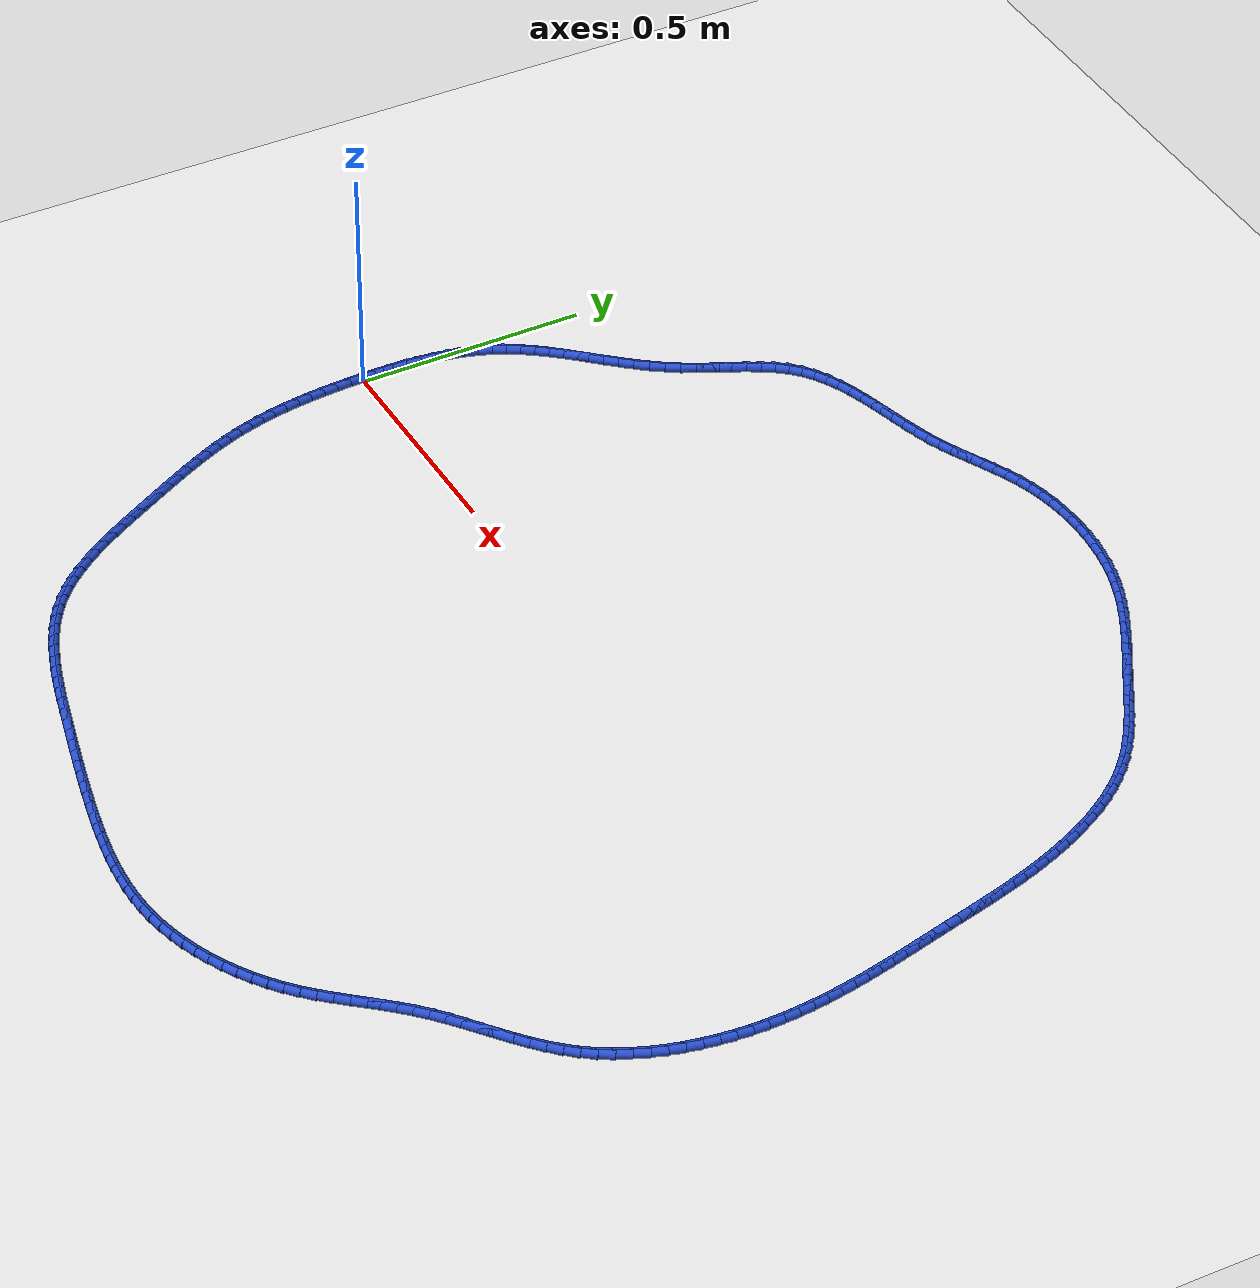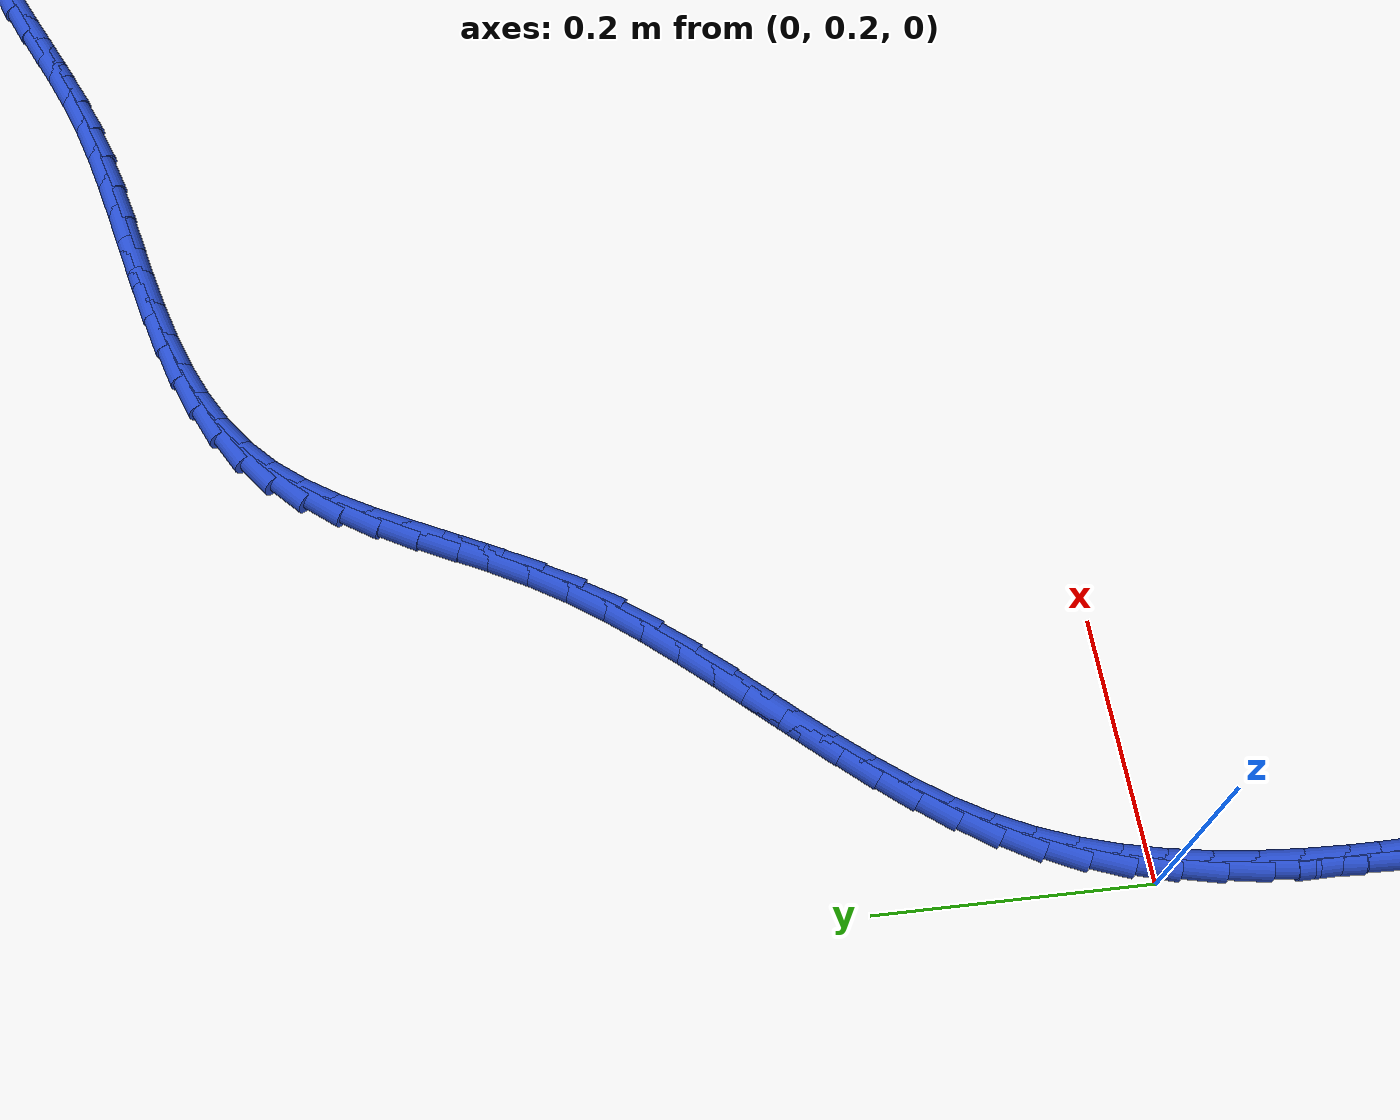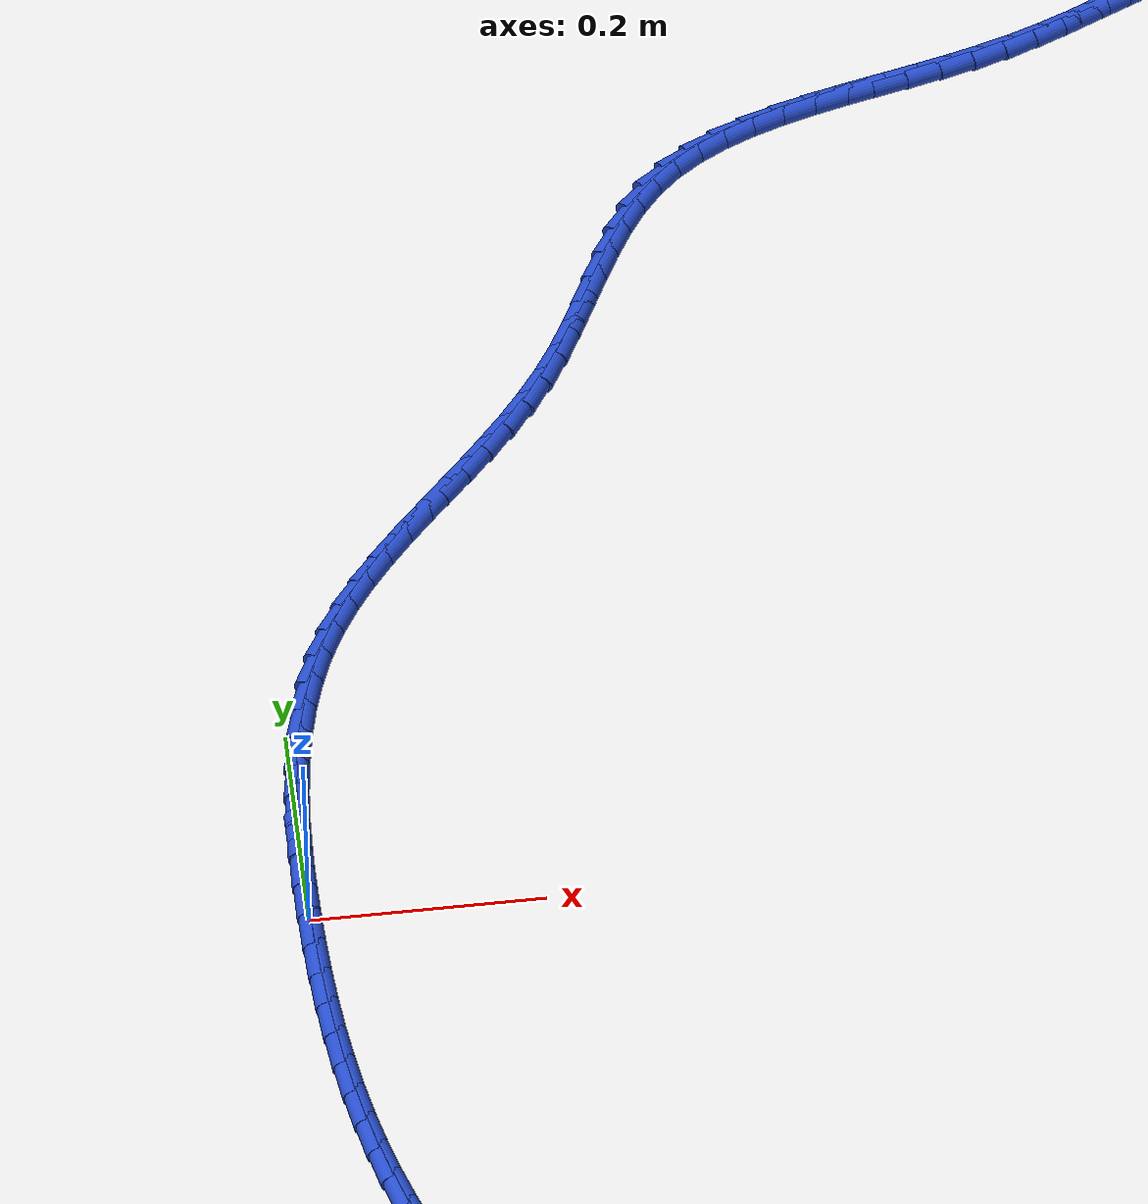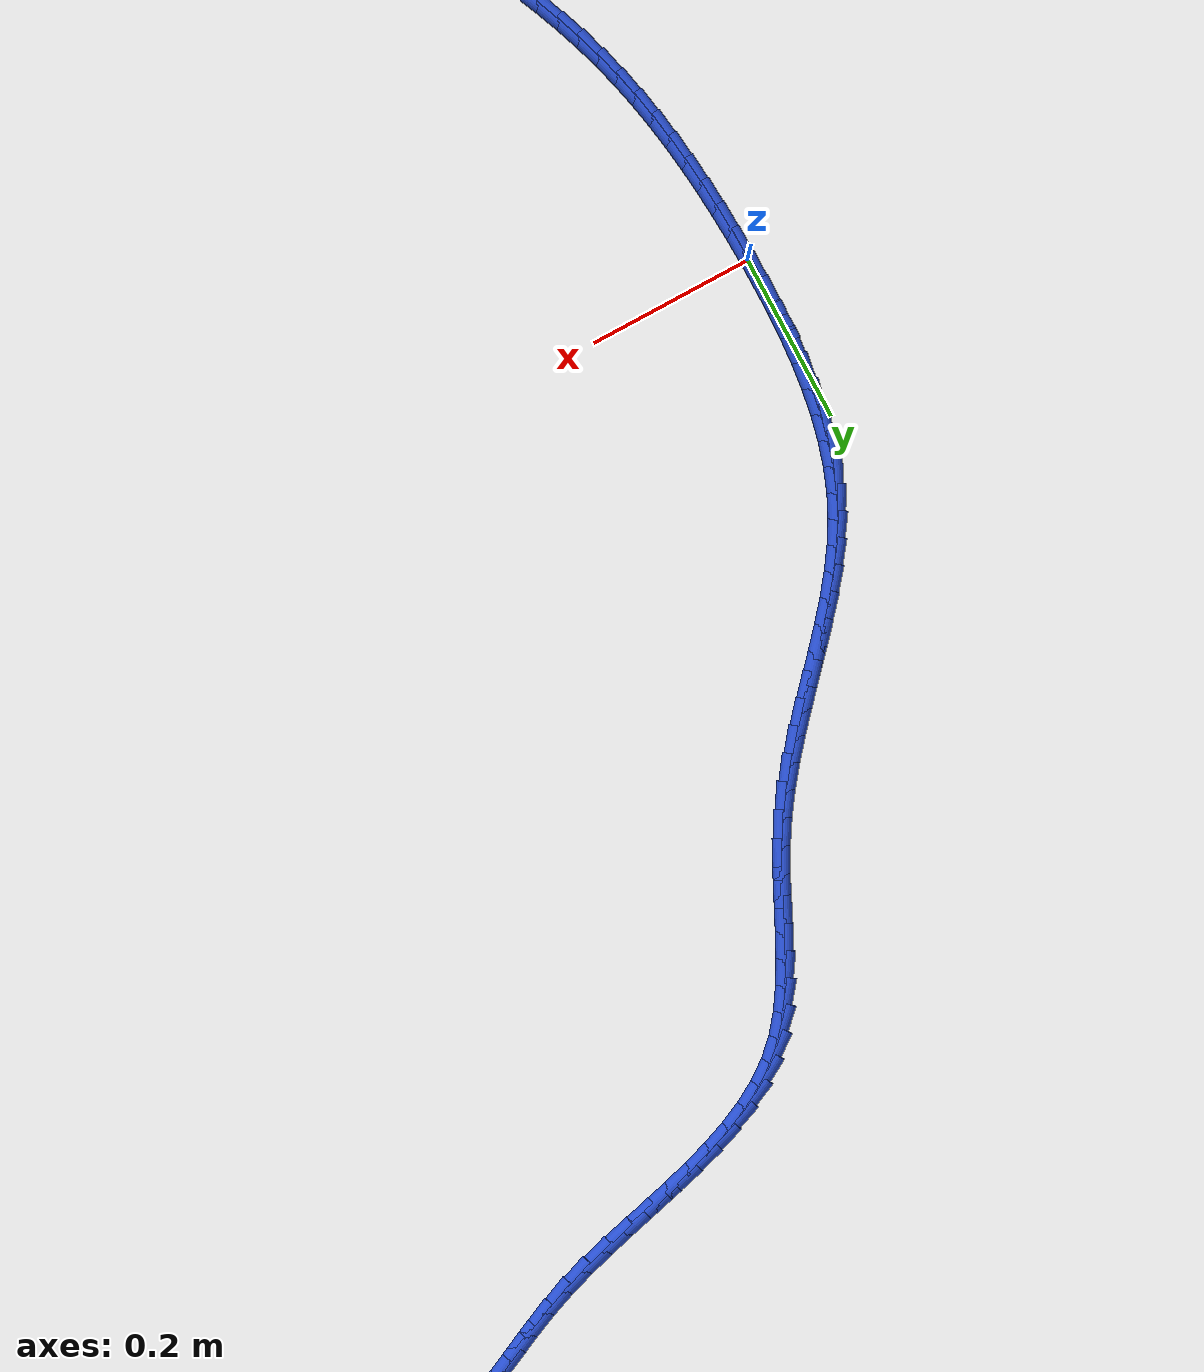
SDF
<sdf version="1.6">
 <world name="default">
  <light name="sun" type="directional">
   <pose>0 0 10 0 -0 0</pose>
   <diffuse>0.8 0.8 0.8 1</diffuse>
   <specular>0.2 0.2 0.2 1</specular>
   <attenuation>
    <range>1000</range>
    <constant>0.9</constant>
    <linear>0.01</linear>
    <quadratic>0.001</quadratic>
   </attenuation>
   <direction>-0.5 0.1 -0.9</direction>
  </light>
  <model name="ground_plane">
   <static>1</static>
   <link name="link">
    <collision name="collision">
     <geometry><plane><normal>0 0 1</normal><size>100 100</size></plane></geometry>
     <surface><friction><ode><mu>100</mu><mu2>50</mu2></ode></friction></surface>
    </collision>
    <visual name="visual">
     <cast_shadows>0</cast_shadows>
     <geometry><plane><normal>0 0 1</normal><size>100 100</size></plane></geometry>
     <material>
      <script><uri>file://media/materials/scripts/gazebo.material</uri><name>Gazebo/WhiteGlow</name></script>
     </material>
    </visual>
   </link>
  </model>
  <gravity>0 0 -9.8</gravity>
  <magnetic_field>6e-06 2.3e-05 -4.2e-05</magnetic_field>
  <atmosphere type="adiabatic"/>
  <physics name="default_physics" default="0" type="ode">
   <max_step_size>0.001</max_step_size>
   <real_time_factor>1</real_time_factor>
   <real_time_update_rate>1000</real_time_update_rate>
  </physics>
  <scene><ambient>0.4 0.4 0.4 1</ambient><background>0.7 0.7 0.7 1</background><shadows>1</shadows></scene>
  <spherical_coordinates>
   <surface_model>EARTH_WGS84</surface_model>
   <latitude_deg>0</latitude_deg>
   <longitude_deg>0</longitude_deg>
   <elevation>0</elevation>
   <heading_deg>0</heading_deg>
  </spherical_coordinates>
  <model name="line">
   <link name="link_0">
    <pose>1.734723475976807e-17 -4.163336342344337e-17 0.01 0 1.57 -1.55265950752404</pose>
    <collision name="collision">
     <geometry><cylinder><radius>0.01</radius><length>0.08</length></cylinder></geometry>
    </collision>
    <visual name="visual">
     <material>
      <script><name>Gazebo/Blue</name><uri>file://media/materials/scripts/gazebo.material</uri></script>
     </material>
     <geometry><cylinder><radius>0.01</radius><length>0.08</length></cylinder></geometry>
    </visual>
   </link>
   <link name="link_1">
    <pose>-0.0005859457003438465 0.03230342886310348 0.01 0 1.57 1.5658201409551833</pose>
    <collision name="collision">
     <geometry><cylinder><radius>0.01</radius><length>0.08</length></cylinder></geometry>
    </collision>
    <visual name="visual">
     <material>
      <script><name>Gazebo/Blue</name><uri>file://media/materials/scripts/gazebo.material</uri></script>
     </material>
     <geometry><cylinder><radius>0.01</radius><length>0.08</length></cylinder></geometry>
    </visual>
   </link>
   <link name="link_2">
    <pose>-0.0004249000776131107 0.06466642707548614 0.01 0 1.57 1.5367646593894932</pose>
    <collision name="collision">
     <geometry><cylinder><radius>0.01</radius><length>0.08</length></cylinder></geometry>
    </collision>
    <visual name="visual">
     <material>
      <script><name>Gazebo/Blue</name><uri>file://media/materials/scripts/gazebo.material</uri></script>
     </material>
     <geometry><cylinder><radius>0.01</radius><length>0.08</length></cylinder></geometry>
    </visual>
   </link>
   <link name="link_3">
    <pose>0.0006735896395232883 0.09693242208971113 0.01 0 1.57 1.501360544168147</pose>
    <collision name="collision">
     <geometry><cylinder><radius>0.01</radius><length>0.08</length></cylinder></geometry>
    </collision>
    <visual name="visual">
     <material>
      <script><name>Gazebo/Blue</name><uri>file://media/materials/scripts/gazebo.material</uri></script>
     </material>
     <geometry><cylinder><radius>0.01</radius><length>0.08</length></cylinder></geometry>
    </visual>
   </link>
   <link name="link_4">
    <pose>0.0028999762223964145 0.12894484135834167 0.01 0 1.57 1.4590960805574682</pose>
    <collision name="collision">
     <geometry><cylinder><radius>0.01</radius><length>0.08</length></cylinder></geometry>
    </collision>
    <visual name="visual">
     <material>
      <script><name>Gazebo/Blue</name><uri>file://media/materials/scripts/gazebo.material</uri></script>
     </material>
     <geometry><cylinder><radius>0.01</radius><length>0.08</length></cylinder></geometry>
    </visual>
   </link>
   <link name="link_5">
    <pose>0.006444712442337328 0.1605471123339411 0.01 0 1.57 1.409382301169204</pose>
    <collision name="collision">
     <geometry><cylinder><radius>0.01</radius><length>0.08</length></cylinder></geometry>
    </collision>
    <visual name="visual">
     <material>
      <script><name>Gazebo/Blue</name><uri>file://media/materials/scripts/gazebo.material</uri></script>
     </material>
     <geometry><cylinder><radius>0.01</radius><length>0.08</length></cylinder></geometry>
    </visual>
   </link>
   <link name="link_6">
    <pose>0.0114982510706771 0.19158266246907257 0.01 0 1.57 1.3516012810251783</pose>
    <collision name="collision">
     <geometry><cylinder><radius>0.01</radius><length>0.08</length></cylinder></geometry>
    </collision>
    <visual name="visual">
     <material>
      <script><name>Gazebo/Blue</name><uri>file://media/materials/scripts/gazebo.material</uri></script>
     </material>
     <geometry><cylinder><radius>0.01</radius><length>0.08</length></cylinder></geometry>
    </visual>
   </link>
   <link name="link_7">
    <pose>0.018251044878746788 0.22189491921629934 0.01 0 1.57 1.2851853566908167</pose>
    <collision name="collision">
     <geometry><cylinder><radius>0.01</radius><length>0.08</length></cylinder></geometry>
    </collision>
    <visual name="visual">
     <material>
      <script><name>Gazebo/Blue</name><uri>file://media/materials/scripts/gazebo.material</uri></script>
     </material>
     <geometry><cylinder><radius>0.01</radius><length>0.08</length></cylinder></geometry>
    </visual>
   </link>
   <link name="link_8">
    <pose>0.02689354663787745 0.2513273100281847 0.01 0 1.57 1.2097373404770093</pose>
    <collision name="collision">
     <geometry><cylinder><radius>0.01</radius><length>0.08</length></cylinder></geometry>
    </collision>
    <visual name="visual">
     <material>
      <script><name>Gazebo/Blue</name><uri>file://media/materials/scripts/gazebo.material</uri></script>
     </material>
     <geometry><cylinder><radius>0.01</radius><length>0.08</length></cylinder></geometry>
    </visual>
   </link>
   <link name="link_9">
    <pose>0.03761620911940015 0.2797232623572918 0.01 0 1.57 1.1255262804051775</pose>
    <collision name="collision">
     <geometry><cylinder><radius>0.01</radius><length>0.08</length></cylinder></geometry>
    </collision>
    <visual name="visual">
     <material>
      <script><name>Gazebo/Blue</name><uri>file://media/materials/scripts/gazebo.material</uri></script>
     </material>
     <geometry><cylinder><radius>0.01</radius><length>0.08</length></cylinder></geometry>
    </visual>
   </link>
   <link name="link_10">
    <pose>0.05060117527124335 0.3069320277369296 0.01 0 1.57 1.042751113733992</pose>
    <collision name="collision">
     <geometry><cylinder><radius>0.01</radius><length>0.08</length></cylinder></geometry>
    </collision>
    <visual name="visual">
     <material>
      <script><name>Gazebo/Blue</name><uri>file://media/materials/scripts/gazebo.material</uri></script>
     </material>
     <geometry><cylinder><radius>0.01</radius><length>0.08</length></cylinder></geometry>
    </visual>
   </link>
   <link name="link_11">
    <pose>0.06578988234074315 0.3329715603753368 0.01 0 1.57 0.9733938336535853</pose>
    <collision name="collision">
     <geometry><cylinder><radius>0.01</radius><length>0.08</length></cylinder></geometry>
    </collision>
    <visual name="visual">
     <material>
      <script><name>Gazebo/Blue</name><uri>file://media/materials/scripts/gazebo.material</uri></script>
     </material>
     <geometry><cylinder><radius>0.01</radius><length>0.08</length></cylinder></geometry>
    </visual>
   </link>
   <link name="link_12">
    <pose>0.0828517972117375 0.3580504295252259 0.01 0 1.57 0.9184853497093782</pose>
    <collision name="collision">
     <geometry><cylinder><radius>0.01</radius><length>0.08</length></cylinder></geometry>
    </collision>
    <visual name="visual">
     <material>
      <script><name>Gazebo/Blue</name><uri>file://media/materials/scripts/gazebo.material</uri></script>
     </material>
     <geometry><cylinder><radius>0.01</radius><length>0.08</length></cylinder></geometry>
    </visual>
   </link>
   <link name="link_13">
    <pose>0.10144179476598855 0.3823874314915847 0.01 0 1.57 0.8778447194304946</pose>
    <collision name="collision">
     <geometry><cylinder><radius>0.01</radius><length>0.08</length></cylinder></geometry>
    </collision>
    <visual name="visual">
     <material>
      <script><name>Gazebo/Blue</name><uri>file://media/materials/scripts/gazebo.material</uri></script>
     </material>
     <geometry><cylinder><radius>0.01</radius><length>0.08</length></cylinder></geometry>
    </visual>
   </link>
   <link name="link_14">
    <pose>0.12121474988525856 0.40620136257940076 0.01 0 1.57 0.8510073917757544</pose>
    <collision name="collision">
     <geometry><cylinder><radius>0.01</radius><length>0.08</length></cylinder></geometry>
    </collision>
    <visual name="visual">
     <material>
      <script><name>Gazebo/Blue</name><uri>file://media/materials/scripts/gazebo.material</uri></script>
     </material>
     <geometry><cylinder><radius>0.01</radius><length>0.08</length></cylinder></geometry>
    </visual>
   </link>
   <link name="link_15">
    <pose>0.14182553745130963 0.42971101909366144 0.01 0 1.57 0.8374688288999654</pose>
    <collision name="collision">
     <geometry><cylinder><radius>0.01</radius><length>0.08</length></cylinder></geometry>
    </collision>
    <visual name="visual">
     <material>
      <script><name>Gazebo/Blue</name><uri>file://media/materials/scripts/gazebo.material</uri></script>
     </material>
     <geometry><cylinder><radius>0.01</radius><length>0.08</length></cylinder></geometry>
    </visual>
   </link>
   <link name="link_16">
    <pose>0.16292903234590386 0.45313519733935437 0.01 0 1.57 0.8368254981185318</pose>
    <collision name="collision">
     <geometry><cylinder><radius>0.01</radius><length>0.08</length></cylinder></geometry>
    </collision>
    <visual name="visual">
     <material>
      <script><name>Gazebo/Blue</name><uri>file://media/materials/scripts/gazebo.material</uri></script>
     </material>
     <geometry><cylinder><radius>0.01</radius><length>0.08</length></cylinder></geometry>
    </visual>
   </link>
   <link name="link_17">
    <pose>0.18418010945080346 0.4766926936214669 0.01 0 1.57 0.8488333265812975</pose>
    <collision name="collision">
     <geometry><cylinder><radius>0.01</radius><length>0.08</length></cylinder></geometry>
    </collision>
    <visual name="visual">
     <material>
      <script><name>Gazebo/Blue</name><uri>file://media/materials/scripts/gazebo.material</uri></script>
     </material>
     <geometry><cylinder><radius>0.01</radius><length>0.08</length></cylinder></geometry>
    </visual>
   </link>
   <link name="link_18">
    <pose>0.20523364364777066 0.5006023042449869 0.01 0 1.57 0.8734017169391491</pose>
    <collision name="collision">
     <geometry><cylinder><radius>0.01</radius><length>0.08</length></cylinder></geometry>
    </collision>
    <visual name="visual">
     <material>
      <script><name>Gazebo/Blue</name><uri>file://media/materials/scripts/gazebo.material</uri></script>
     </material>
     <geometry><cylinder><radius>0.01</radius><length>0.08</length></cylinder></geometry>
    </visual>
   </link>
   <link name="link_19">
    <pose>0.22574450981856753 0.5250828255149016 0.01 0 1.57 0.9105315166691059</pose>
    <collision name="collision">
     <geometry><cylinder><radius>0.01</radius><length>0.08</length></cylinder></geometry>
    </collision>
    <visual name="visual">
     <material>
      <script><name>Gazebo/Blue</name><uri>file://media/materials/scripts/gazebo.material</uri></script>
     </material>
     <geometry><cylinder><radius>0.01</radius><length>0.08</length></cylinder></geometry>
    </visual>
   </link>
   <link name="link_20">
    <pose>0.24536758284495633 0.5503530537361989 0.01 0 1.57 0.960196978948396</pose>
    <collision name="collision">
     <geometry><cylinder><radius>0.01</radius><length>0.08</length></cylinder></geometry>
    </collision>
    <visual name="visual">
     <material>
      <script><name>Gazebo/Blue</name><uri>file://media/materials/scripts/gazebo.material</uri></script>
     </material>
     <geometry><cylinder><radius>0.01</radius><length>0.08</length></cylinder></geometry>
    </visual>
   </link>
   <link name="link_21">
    <pose>0.26375773760869914 0.576631785213866 0.01 0 1.57 1.0216188614000867</pose>
    <collision name="collision">
     <geometry><cylinder><radius>0.01</radius><length>0.08</length></cylinder></geometry>
    </collision>
    <visual name="visual">
     <material>
      <script><name>Gazebo/Blue</name><uri>file://media/materials/scripts/gazebo.material</uri></script>
     </material>
     <geometry><cylinder><radius>0.01</radius><length>0.08</length></cylinder></geometry>
    </visual>
   </link>
   <link name="link_22">
    <pose>0.280583520935067 0.6041260605972684 0.01 0 1.57 1.0779718395992874</pose>
    <collision name="collision">
     <geometry><cylinder><radius>0.01</radius><length>0.08</length></cylinder></geometry>
    </collision>
    <visual name="visual">
     <material>
      <script><name>Gazebo/Blue</name><uri>file://media/materials/scripts/gazebo.material</uri></script>
     </material>
     <geometry><cylinder><radius>0.01</radius><length>0.08</length></cylinder></geometry>
    </visual>
   </link>
   <link name="link_23">
    <pose>0.2959232772794741 0.6326905609892598 0.01 0 1.57 1.110982557753976</pose>
    <collision name="collision">
     <geometry><cylinder><radius>0.01</radius><length>0.08</length></cylinder></geometry>
    </collision>
    <visual name="visual">
     <material>
      <script><name>Gazebo/Blue</name><uri>file://media/materials/scripts/gazebo.material</uri></script>
     </material>
     <geometry><cylinder><radius>0.01</radius><length>0.08</length></cylinder></geometry>
    </visual>
   </link>
   <link name="link_24">
    <pose>0.3103263667475937 0.6617749703704134 0.01 0 1.57 1.1202969607023132</pose>
    <collision name="collision">
     <geometry><cylinder><radius>0.01</radius><length>0.08</length></cylinder></geometry>
    </collision>
    <visual name="visual">
     <material>
      <script><name>Gazebo/Blue</name><uri>file://media/materials/scripts/gazebo.material</uri></script>
     </material>
     <geometry><cylinder><radius>0.01</radius><length>0.08</length></cylinder></geometry>
    </visual>
   </link>
   <link name="link_25">
    <pose>0.32436813944007176 0.6908066255377934 0.01 0 1.57 1.1056659999793053</pose>
    <collision name="collision">
     <geometry><cylinder><radius>0.01</radius><length>0.08</length></cylinder></geometry>
    </collision>
    <visual name="visual">
     <material>
      <script><name>Gazebo/Blue</name><uri>file://media/materials/scripts/gazebo.material</uri></script>
     </material>
     <geometry><cylinder><radius>0.01</radius><length>0.08</length></cylinder></geometry>
    </visual>
   </link>
   <link name="link_26">
    <pose>0.3386239454575542 0.719212863288464 0.01 0 1.57 1.06567870682173</pose>
    <collision name="collision">
     <geometry><cylinder><radius>0.01</radius><length>0.08</length></cylinder></geometry>
    </collision>
    <visual name="visual">
     <material>
      <script><name>Gazebo/Blue</name><uri>file://media/materials/scripts/gazebo.material</uri></script>
     </material>
     <geometry><cylinder><radius>0.01</radius><length>0.08</length></cylinder></geometry>
    </visual>
   </link>
   <link name="link_27">
    <pose>0.3536691349006872 0.7464210204194895 0.01 0 1.57 0.9978665875913788</pose>
    <collision name="collision">
     <geometry><cylinder><radius>0.01</radius><length>0.08</length></cylinder></geometry>
    </collision>
    <visual name="visual">
     <material>
      <script><name>Gazebo/Blue</name><uri>file://media/materials/scripts/gazebo.material</uri></script>
     </material>
     <geometry><cylinder><radius>0.01</radius><length>0.08</length></cylinder></geometry>
    </visual>
   </link>
   <link name="link_28">
    <pose>0.37007905787011636 0.7718584337279338 0.01 0 1.57 0.8993697789487483</pose>
    <collision name="collision">
     <geometry><cylinder><radius>0.01</radius><length>0.08</length></cylinder></geometry>
    </collision>
    <visual name="visual">
     <material>
      <script><name>Gazebo/Blue</name><uri>file://media/materials/scripts/gazebo.material</uri></script>
     </material>
     <geometry><cylinder><radius>0.01</radius><length>0.08</length></cylinder></geometry>
    </visual>
   </link>
   <link name="link_29">
    <pose>0.38842906446648784 0.7949524400108614 0.01 0 1.57 0.77045522675812</pose>
    <collision name="collision">
     <geometry><cylinder><radius>0.01</radius><length>0.08</length></cylinder></geometry>
    </collision>
    <visual name="visual">
     <material>
      <script><name>Gazebo/Blue</name><uri>file://media/materials/scripts/gazebo.material</uri></script>
     </material>
     <geometry><cylinder><radius>0.01</radius><length>0.08</length></cylinder></geometry>
    </visual>
   </link>
   <link name="link_30">
    <pose>0.409258775442597 0.8151687571339272 0.01 0 1.57 0.6385212311420206</pose>
    <collision name="collision">
     <geometry><cylinder><radius>0.01</radius><length>0.08</length></cylinder></geometry>
    </collision>
    <visual name="visual">
     <material>
      <script><name>Gazebo/Blue</name><uri>file://media/materials/scripts/gazebo.material</uri></script>
     </material>
     <geometry><cylinder><radius>0.01</radius><length>0.08</length></cylinder></geometry>
    </visual>
   </link>
   <link name="link_31">
    <pose>0.4326136926827654 0.8325038937922786 0.01 0 1.57 0.5258831245029496</pose>
    <collision name="collision">
     <geometry><cylinder><radius>0.01</radius><length>0.08</length></cylinder></geometry>
    </collision>
    <visual name="visual">
     <material>
      <script><name>Gazebo/Blue</name><uri>file://media/materials/scripts/gazebo.material</uri></script>
     </material>
     <geometry><cylinder><radius>0.01</radius><length>0.08</length></cylinder></geometry>
    </visual>
   </link>
   <link name="link_32">
    <pose>0.45817864815941817 0.8473417963887165 0.01 0 1.57 0.43431166738604354</pose>
    <collision name="collision">
     <geometry><cylinder><radius>0.01</radius><length>0.08</length></cylinder></geometry>
    </collision>
    <visual name="visual">
     <material>
      <script><name>Gazebo/Blue</name><uri>file://media/materials/scripts/gazebo.material</uri></script>
     </material>
     <geometry><cylinder><radius>0.01</radius><length>0.08</length></cylinder></geometry>
    </visual>
   </link>
   <link name="link_33">
    <pose>0.4856302662462879 0.8600752280671036 0.01 0 1.57 0.3630283458589276</pose>
    <collision name="collision">
     <geometry><cylinder><radius>0.01</radius><length>0.08</length></cylinder></geometry>
    </collision>
    <visual name="visual">
     <material>
      <script><name>Gazebo/Blue</name><uri>file://media/materials/scripts/gazebo.material</uri></script>
     </material>
     <geometry><cylinder><radius>0.01</radius><length>0.08</length></cylinder></geometry>
    </visual>
   </link>
   <link name="link_34">
    <pose>0.5146451713171074 0.871096951971303 0.01 0 1.57 0.3103395812686688</pose>
    <collision name="collision">
     <geometry><cylinder><radius>0.01</radius><length>0.08</length></cylinder></geometry>
    </collision>
    <visual name="visual">
     <material>
      <script><name>Gazebo/Blue</name><uri>file://media/materials/scripts/gazebo.material</uri></script>
     </material>
     <geometry><cylinder><radius>0.01</radius><length>0.08</length></cylinder></geometry>
    </visual>
   </link>
   <link name="link_35">
    <pose>0.5448999877456098 0.8807997312451785 0.01 0 1.57 0.2744544623593206</pose>
    <collision name="collision">
     <geometry><cylinder><radius>0.01</radius><length>0.08</length></cylinder></geometry>
    </collision>
    <visual name="visual">
     <material>
      <script><name>Gazebo/Blue</name><uri>file://media/materials/scripts/gazebo.material</uri></script>
     </material>
     <geometry><cylinder><radius>0.01</radius><length>0.08</length></cylinder></geometry>
    </visual>
   </link>
   <link name="link_36">
    <pose>0.5760713399055274 0.8895763290325926 0.01 0 1.57 0.25390817112056835</pose>
    <collision name="collision">
     <geometry><cylinder><radius>0.01</radius><length>0.08</length></cylinder></geometry>
    </collision>
    <visual name="visual">
     <material>
      <script><name>Gazebo/Blue</name><uri>file://media/materials/scripts/gazebo.material</uri></script>
     </material>
     <geometry><cylinder><radius>0.01</radius><length>0.08</length></cylinder></geometry>
    </visual>
   </link>
   <link name="link_37">
    <pose>0.6078358521705939 0.8978195084774098 0.01 0 1.57 0.2477370313288137</pose>
    <collision name="collision">
     <geometry><cylinder><radius>0.01</radius><length>0.08</length></cylinder></geometry>
    </collision>
    <visual name="visual">
     <material>
      <script><name>Gazebo/Blue</name><uri>file://media/materials/scripts/gazebo.material</uri></script>
     </material>
     <geometry><cylinder><radius>0.01</radius><length>0.08</length></cylinder></geometry>
    </visual>
   </link>
   <link name="link_38">
    <pose>0.6398701489145413 0.905922032723492 0.01 0 1.57 0.255528976271041</pose>
    <collision name="collision">
     <geometry><cylinder><radius>0.01</radius><length>0.08</length></cylinder></geometry>
    </collision>
    <visual name="visual">
     <material>
      <script><name>Gazebo/Blue</name><uri>file://media/materials/scripts/gazebo.material</uri></script>
     </material>
     <geometry><cylinder><radius>0.01</radius><length>0.08</length></cylinder></geometry>
    </visual>
   </link>
   <link name="link_39">
    <pose>0.6718508545111028 0.9142766649147034 0.01 0 1.57 0.277417834478141</pose>
    <collision name="collision">
     <geometry><cylinder><radius>0.01</radius><length>0.08</length></cylinder></geometry>
    </collision>
    <visual name="visual">
     <material>
      <script><name>Gazebo/Blue</name><uri>file://media/materials/scripts/gazebo.material</uri></script>
     </material>
     <geometry><cylinder><radius>0.01</radius><length>0.08</length></cylinder></geometry>
    </visual>
   </link>
   <link name="link_40">
    <pose>0.7034545933340117 0.923276168194907 0.01 0 1.57 0.31404263416070194</pose>
    <collision name="collision">
     <geometry><cylinder><radius>0.01</radius><length>0.08</length></cylinder></geometry>
    </collision>
    <visual name="visual">
     <material>
      <script><name>Gazebo/Blue</name><uri>file://media/materials/scripts/gazebo.material</uri></script>
     </material>
     <geometry><cylinder><radius>0.01</radius><length>0.08</length></cylinder></geometry>
    </visual>
   </link>
   <link name="link_41">
    <pose>0.7343579897570004 0.9333133057079659 0.01 0 1.57 0.3643122296036999</pose>
    <collision name="collision">
     <geometry><cylinder><radius>0.01</radius><length>0.08</length></cylinder></geometry>
    </collision>
    <visual name="visual">
     <material>
      <script><name>Gazebo/Blue</name><uri>file://media/materials/scripts/gazebo.material</uri></script>
     </material>
     <geometry><cylinder><radius>0.01</radius><length>0.08</length></cylinder></geometry>
    </visual>
   </link>
   <link name="link_42">
    <pose>0.7642777164148208 0.9447227168082878 0.01 0 1.57 0.4088945234355263</pose>
    <collision name="collision">
     <geometry><cylinder><radius>0.01</radius><length>0.08</length></cylinder></geometry>
    </collision>
    <visual name="visual">
     <material>
      <script><name>Gazebo/Blue</name><uri>file://media/materials/scripts/gazebo.material</uri></script>
     </material>
     <geometry><cylinder><radius>0.01</radius><length>0.08</length></cylinder></geometry>
    </visual>
   </link>
   <link name="link_43">
    <pose>0.7933021807018763 0.9572995259661532 0.01 0 1.57 0.4361726385905524</pose>
    <collision name="collision">
     <geometry><cylinder><radius>0.01</radius><length>0.08</length></cylinder></geometry>
    </collision>
    <visual name="visual">
     <material>
      <script><name>Gazebo/Blue</name><uri>file://media/materials/scripts/gazebo.material</uri></script>
     </material>
     <geometry><cylinder><radius>0.01</radius><length>0.08</length></cylinder></geometry>
    </visual>
   </link>
   <link name="link_44">
    <pose>0.8217214786667539 0.9705461381036493 0.01 0 1.57 0.44534689665823335</pose>
    <collision name="collision">
     <geometry><cylinder><radius>0.01</radius><length>0.08</length></cylinder></geometry>
    </collision>
    <visual name="visual">
     <material>
      <script><name>Gazebo/Blue</name><uri>file://media/materials/scripts/gazebo.material</uri></script>
     </material>
     <geometry><cylinder><radius>0.01</radius><length>0.08</length></cylinder></geometry>
    </visual>
   </link>
   <link name="link_45">
    <pose>0.849827705871831 0.9839620561612165 0.01 0 1.57 0.4359917959759961</pose>
    <collision name="collision">
     <geometry><cylinder><radius>0.01</radius><length>0.08</length></cylinder></geometry>
    </collision>
    <visual name="visual">
     <material>
      <script><name>Gazebo/Blue</name><uri>file://media/materials/scripts/gazebo.material</uri></script>
     </material>
     <geometry><cylinder><radius>0.01</radius><length>0.08</length></cylinder></geometry>
    </visual>
   </link>
   <link name="link_46">
    <pose>0.8779129578794848 0.997046783079294 0.01 0 1.57 0.40787644396506917</pose>
    <collision name="collision">
     <geometry><cylinder><radius>0.01</radius><length>0.08</length></cylinder></geometry>
    </collision>
    <visual name="visual">
     <material>
      <script><name>Gazebo/Blue</name><uri>file://media/materials/scripts/gazebo.material</uri></script>
     </material>
     <geometry><cylinder><radius>0.01</radius><length>0.08</length></cylinder></geometry>
    </visual>
   </link>
   <link name="link_47">
    <pose>0.9062693302520927 1.0092998217983216 0.01 0 1.57 0.36107289424932015</pose>
    <collision name="collision">
     <geometry><cylinder><radius>0.01</radius><length>0.08</length></cylinder></geometry>
    </collision>
    <visual name="visual">
     <material>
      <script><name>Gazebo/Blue</name><uri>file://media/materials/scripts/gazebo.material</uri></script>
     </material>
     <geometry><cylinder><radius>0.01</radius><length>0.08</length></cylinder></geometry>
    </visual>
   </link>
   <link name="link_48">
    <pose>0.9351889185520318 1.0202206752587393 0.01 0 1.57 0.29907786903546074</pose>
    <collision name="collision">
     <geometry><cylinder><radius>0.01</radius><length>0.08</length></cylinder></geometry>
    </collision>
    <visual name="visual">
     <material>
      <script><name>Gazebo/Blue</name><uri>file://media/materials/scripts/gazebo.material</uri></script>
     </material>
     <geometry><cylinder><radius>0.01</radius><length>0.08</length></cylinder></geometry>
    </visual>
   </link>
   <link name="link_49">
    <pose>0.9649033268434378 1.0293824049245281 0.01 0 1.57 0.23609268102748873</pose>
    <collision name="collision">
     <geometry><cylinder><radius>0.01</radius><length>0.08</length></cylinder></geometry>
    </collision>
    <visual name="visual">
     <material>
      <script><name>Gazebo/Blue</name><uri>file://media/materials/scripts/gazebo.material</uri></script>
     </material>
     <geometry><cylinder><radius>0.01</radius><length>0.08</length></cylinder></geometry>
    </visual>
   </link>
   <link name="link_50">
    <pose>0.9953558554791279 1.0367086536794146 0.01 0 1.57 0.17591055692172775</pose>
    <collision name="collision">
     <geometry><cylinder><radius>0.01</radius><length>0.08</length></cylinder></geometry>
    </collision>
    <visual name="visual">
     <material>
      <script><name>Gazebo/Blue</name><uri>file://media/materials/scripts/gazebo.material</uri></script>
     </material>
     <geometry><cylinder><radius>0.01</radius><length>0.08</length></cylinder></geometry>
    </visual>
   </link>
   <link name="link_51">
    <pose>1.0264040082564816 1.0422273942406821 0.01 0 1.57 0.11814787920801474</pose>
    <collision name="collision">
     <geometry><cylinder><radius>0.01</radius><length>0.08</length></cylinder></geometry>
    </collision>
    <visual name="visual">
     <material>
      <script><name>Gazebo/Blue</name><uri>file://media/materials/scripts/gazebo.material</uri></script>
     </material>
     <geometry><cylinder><radius>0.01</radius><length>0.08</length></cylinder></geometry>
    </visual>
   </link>
   <link name="link_52">
    <pose>1.057905274626059 1.0459666167715465 0.01 0 1.57 0.06240167657679977</pose>
    <collision name="collision">
     <geometry><cylinder><radius>0.01</radius><length>0.08</length></cylinder></geometry>
    </collision>
    <visual name="visual">
     <material>
      <script><name>Gazebo/Blue</name><uri>file://media/materials/scripts/gazebo.material</uri></script>
     </material>
     <geometry><cylinder><radius>0.01</radius><length>0.08</length></cylinder></geometry>
    </visual>
   </link>
   <link name="link_53">
    <pose>1.089717144038422 1.0479543114352259 0.01 0 1.57 0.00825988952160205</pose>
    <collision name="collision">
     <geometry><cylinder><radius>0.01</radius><length>0.08</length></cylinder></geometry>
    </collision>
    <visual name="visual">
     <material>
      <script><name>Gazebo/Blue</name><uri>file://media/materials/scripts/gazebo.material</uri></script>
     </material>
     <geometry><cylinder><radius>0.01</radius><length>0.08</length></cylinder></geometry>
    </visual>
   </link>
   <link name="link_54">
    <pose>1.1216971059441296 1.0482184683949372 0.01 0 1.57 -0.044693425369481066</pose>
    <collision name="collision">
     <geometry><cylinder><radius>0.01</radius><length>0.08</length></cylinder></geometry>
    </collision>
    <visual name="visual">
     <material>
      <script><name>Gazebo/Blue</name><uri>file://media/materials/scripts/gazebo.material</uri></script>
     </material>
     <geometry><cylinder><radius>0.01</radius><length>0.08</length></cylinder></geometry>
    </visual>
   </link>
   <link name="link_55">
    <pose>1.1537026497937446 1.046787077813898 0.01 0 1.57 -0.09687618377099172</pose>
    <collision name="collision">
     <geometry><cylinder><radius>0.01</radius><length>0.08</length></cylinder></geometry>
    </collision>
    <visual name="visual">
     <material>
      <script><name>Gazebo/Blue</name><uri>file://media/materials/scripts/gazebo.material</uri></script>
     </material>
     <geometry><cylinder><radius>0.01</radius><length>0.08</length></cylinder></geometry>
    </visual>
   </link>
   <link name="link_56">
    <pose>1.1855912650378266 1.0436881298553242 0.01 0 1.57 -0.14870870924018223</pose>
    <collision name="collision">
     <geometry><cylinder><radius>0.01</radius><length>0.08</length></cylinder></geometry>
    </collision>
    <visual name="visual">
     <material>
      <script><name>Gazebo/Blue</name><uri>file://media/materials/scripts/gazebo.material</uri></script>
     </material>
     <geometry><cylinder><radius>0.01</radius><length>0.08</length></cylinder></geometry>
    </visual>
   </link>
   <link name="link_57">
    <pose>1.2172204411269365 1.0389496146824335 0.01 0 1.57 -0.20061572777143358</pose>
    <collision name="collision">
     <geometry><cylinder><radius>0.01</radius><length>0.08</length></cylinder></geometry>
    </collision>
    <visual name="visual">
     <material>
      <script><name>Gazebo/Blue</name><uri>file://media/materials/scripts/gazebo.material</uri></script>
     </material>
     <geometry><cylinder><radius>0.01</radius><length>0.08</length></cylinder></geometry>
    </visual>
   </link>
   <link name="link_58">
    <pose>1.2484476675116352 1.0325995224584432 0.01 0 1.57 -0.2530292478597628</pose>
    <collision name="collision">
     <geometry><cylinder><radius>0.01</radius><length>0.08</length></cylinder></geometry>
    </collision>
    <visual name="visual">
     <material>
      <script><name>Gazebo/Blue</name><uri>file://media/materials/scripts/gazebo.material</uri></script>
     </material>
     <geometry><cylinder><radius>0.01</radius><length>0.08</length></cylinder></geometry>
    </visual>
   </link>
   <link name="link_59">
    <pose>1.279130433642484 1.0246658433465707 0.01 0 1.57 -0.3062944268016827</pose>
    <collision name="collision">
     <geometry><cylinder><radius>0.01</radius><length>0.08</length></cylinder></geometry>
    </collision>
    <visual name="visual">
     <material>
      <script><name>Gazebo/Blue</name><uri>file://media/materials/scripts/gazebo.material</uri></script>
     </material>
     <geometry><cylinder><radius>0.01</radius><length>0.08</length></cylinder></geometry>
    </visual>
   </link>
   <link name="link_60">
    <pose>1.3091296381765127 1.0151786990245255 0.01 0 1.57 -0.35765296409318464</pose>
    <collision name="collision">
     <geometry><cylinder><radius>0.01</radius><length>0.08</length></cylinder></geometry>
    </collision>
    <visual name="visual">
     <material>
      <script><name>Gazebo/Blue</name><uri>file://media/materials/scripts/gazebo.material</uri></script>
     </material>
     <geometry><cylinder><radius>0.01</radius><length>0.08</length></cylinder></geometry>
    </visual>
   </link>
   <link name="link_61">
    <pose>1.338412757697989 1.0042348461475807 0.01 0 1.57 -0.403208440867464</pose>
    <collision name="collision">
     <geometry><cylinder><radius>0.01</radius><length>0.08</length></cylinder></geometry>
    </collision>
    <visual name="visual">
     <material>
      <script><name>Gazebo/Blue</name><uri>file://media/materials/scripts/gazebo.material</uri></script>
     </material>
     <geometry><cylinder><radius>0.01</radius><length>0.08</length></cylinder></geometry>
    </visual>
   </link>
   <link name="link_62">
    <pose>1.3670723335773254 0.9920092347590246 0.01 0 1.57 -0.442389218728154</pose>
    <collision name="collision">
     <geometry><cylinder><radius>0.01</radius><length>0.08</length></cylinder></geometry>
    </collision>
    <visual name="visual">
     <material>
      <script><name>Gazebo/Blue</name><uri>file://media/materials/scripts/gazebo.material</uri></script>
     </material>
     <geometry><cylinder><radius>0.01</radius><length>0.08</length></cylinder></geometry>
    </visual>
   </link>
   <link name="link_63">
    <pose>1.3952080434434846 0.9786812766555373 0.01 0 1.57 -0.47498944959321354</pose>
    <collision name="collision">
     <geometry><cylinder><radius>0.01</radius><length>0.08</length></cylinder></geometry>
    </collision>
    <visual name="visual">
     <material>
      <script><name>Gazebo/Blue</name><uri>file://media/materials/scripts/gazebo.material</uri></script>
     </material>
     <geometry><cylinder><radius>0.01</radius><length>0.08</length></cylinder></geometry>
    </visual>
   </link>
   <link name="link_64">
    <pose>1.4229195649254285 0.9644303836337998 0.01 0 1.57 -0.5009225792779068</pose>
    <collision name="collision">
     <geometry><cylinder><radius>0.01</radius><length>0.08</length></cylinder></geometry>
    </collision>
    <visual name="visual">
     <material>
      <script><name>Gazebo/Blue</name><uri>file://media/materials/scripts/gazebo.material</uri></script>
     </material>
     <geometry><cylinder><radius>0.01</radius><length>0.08</length></cylinder></geometry>
    </visual>
   </link>
   <link name="link_65">
    <pose>1.4503065756521196 0.9494359674904927 0.01 0 1.57 -0.5201802405362448</pose>
    <collision name="collision">
     <geometry><cylinder><radius>0.01</radius><length>0.08</length></cylinder></geometry>
    </collision>
    <visual name="visual">
     <material>
      <script><name>Gazebo/Blue</name><uri>file://media/materials/scripts/gazebo.material</uri></script>
     </material>
     <geometry><cylinder><radius>0.01</radius><length>0.08</length></cylinder></geometry>
    </visual>
   </link>
   <link name="link_66">
    <pose>1.4774687532525212 0.9338774400222963 0.01 0 1.57 -0.5327976883712991</pose>
    <collision name="collision">
     <geometry><cylinder><radius>0.01</radius><length>0.08</length></cylinder></geometry>
    </collision>
    <visual name="visual">
     <material>
      <script><name>Gazebo/Blue</name><uri>file://media/materials/scripts/gazebo.material</uri></script>
     </material>
     <geometry><cylinder><radius>0.01</radius><length>0.08</length></cylinder></geometry>
    </visual>
   </link>
   <link name="link_67">
    <pose>1.5045057753555953 0.9179342130258914 0.01 0 1.57 -0.538827927405153</pose>
    <collision name="collision">
     <geometry><cylinder><radius>0.01</radius><length>0.08</length></cylinder></geometry>
    </collision>
    <visual name="visual">
     <material>
      <script><name>Gazebo/Blue</name><uri>file://media/materials/scripts/gazebo.material</uri></script>
     </material>
     <geometry><cylinder><radius>0.01</radius><length>0.08</length></cylinder></geometry>
    </visual>
   </link>
   <link name="link_68">
    <pose>1.531517319590305 0.9017856982979588 0.01 0 1.57 -0.5383253404514637</pose>
    <collision name="collision">
     <geometry><cylinder><radius>0.01</radius><length>0.08</length></cylinder></geometry>
    </collision>
    <visual name="visual">
     <material>
      <script><name>Gazebo/Blue</name><uri>file://media/materials/scripts/gazebo.material</uri></script>
     </material>
     <geometry><cylinder><radius>0.01</radius><length>0.08</length></cylinder></geometry>
    </visual>
   </link>
   <link name="link_69">
    <pose>1.5586030579915682 0.8856113002994913 0.01 0 1.57 -0.5340646747950105</pose>
    <collision name="collision">
     <geometry><cylinder><radius>0.01</radius><length>0.08</length></cylinder></geometry>
    </collision>
    <visual name="visual">
     <material>
      <script><name>Gazebo/Blue</name><uri>file://media/materials/scripts/gazebo.material</uri></script>
     </material>
     <geometry><cylinder><radius>0.01</radius><length>0.08</length></cylinder></geometry>
    </visual>
   </link>
   <link name="link_70">
    <pose>1.585810009356946 0.8695213772529206 0.01 0 1.57 -0.5354538713124185</pose>
    <collision name="collision">
     <geometry><cylinder><radius>0.01</radius><length>0.08</length></cylinder></geometry>
    </collision>
    <visual name="visual">
     <material>
      <script><name>Gazebo/Blue</name><uri>file://media/materials/scripts/gazebo.material</uri></script>
     </material>
     <geometry><cylinder><radius>0.01</radius><length>0.08</length></cylinder></geometry>
    </visual>
   </link>
   <link name="link_71">
    <pose>1.6130036871650109 0.8533882723946312 0.01 0 1.57 -0.5445229784399765</pose>
    <collision name="collision">
     <geometry><cylinder><radius>0.01</radius><length>0.08</length></cylinder></geometry>
    </collision>
    <visual name="visual">
     <material>
      <script><name>Gazebo/Blue</name><uri>file://media/materials/scripts/gazebo.material</uri></script>
     </material>
     <geometry><cylinder><radius>0.01</radius><length>0.08</length></cylinder></geometry>
    </visual>
   </link>
   <link name="link_72">
    <pose>1.6400105234315538 0.8370330799184423 0.01 0 1.57 -0.5613517820341806</pose>
    <collision name="collision">
     <geometry><cylinder><radius>0.01</radius><length>0.08</length></cylinder></geometry>
    </collision>
    <visual name="visual">
     <material>
      <script><name>Gazebo/Blue</name><uri>file://media/materials/scripts/gazebo.material</uri></script>
     </material>
     <geometry><cylinder><radius>0.01</radius><length>0.08</length></cylinder></geometry>
    </visual>
   </link>
   <link name="link_73">
    <pose>1.6666569501723658 0.8202768940181727 0.01 0 1.57 -0.5860855720560209</pose>
    <collision name="collision">
     <geometry><cylinder><radius>0.01</radius><length>0.08</length></cylinder></geometry>
    </collision>
    <visual name="visual">
     <material>
      <script><name>Gazebo/Blue</name><uri>file://media/materials/scripts/gazebo.material</uri></script>
     </material>
     <geometry><cylinder><radius>0.01</radius><length>0.08</length></cylinder></geometry>
    </visual>
   </link>
   <link name="link_74">
    <pose>1.692769399403237 0.8029408088876421 0.01 0 1.57 -0.6189066775130571</pose>
    <collision name="collision">
     <geometry><cylinder><radius>0.01</radius><length>0.08</length></cylinder></geometry>
    </collision>
    <visual name="visual">
     <material>
      <script><name>Gazebo/Blue</name><uri>file://media/materials/scripts/gazebo.material</uri></script>
     </material>
     <geometry><cylinder><radius>0.01</radius><length>0.08</length></cylinder></geometry>
    </visual>
   </link>
   <link name="link_75">
    <pose>1.7181743031399594 0.7848459187206697 0.01 0 1.57 -0.6599889784825738</pose>
    <collision name="collision">
     <geometry><cylinder><radius>0.01</radius><length>0.08</length></cylinder></geometry>
    </collision>
    <visual name="visual">
     <material>
      <script><name>Gazebo/Blue</name><uri>file://media/materials/scripts/gazebo.material</uri></script>
     </material>
     <geometry><cylinder><radius>0.01</radius><length>0.08</length></cylinder></geometry>
    </visual>
   </link>
   <link name="link_76">
    <pose>1.7426980933983238 0.7658133177110741 0.01 0 1.57 -0.7094323298311118</pose>
    <collision name="collision">
     <geometry><cylinder><radius>0.01</radius><length>0.08</length></cylinder></geometry>
    </collision>
    <visual name="visual">
     <material>
      <script><name>Gazebo/Blue</name><uri>file://media/materials/scripts/gazebo.material</uri></script>
     </material>
     <geometry><cylinder><radius>0.01</radius><length>0.08</length></cylinder></geometry>
    </visual>
   </link>
   <link name="link_77">
    <pose>1.7661672021941195 0.7456641000526749 0.01 0 1.57 -0.7671541768516821</pose>
    <collision name="collision">
     <geometry><cylinder><radius>0.01</radius><length>0.08</length></cylinder></geometry>
    </collision>
    <visual name="visual">
     <material>
      <script><name>Gazebo/Blue</name><uri>file://media/materials/scripts/gazebo.material</uri></script>
     </material>
     <geometry><cylinder><radius>0.01</radius><length>0.08</length></cylinder></geometry>
    </visual>
   </link>
   <link name="link_78">
    <pose>1.7884084698463087 0.7242199176011412 0.01 0 1.57 -0.8292669303699153</pose>
    <collision name="collision">
     <geometry><cylinder><radius>0.01</radius><length>0.08</length></cylinder></geometry>
    </collision>
    <visual name="visual">
     <material>
      <script><name>Gazebo/Blue</name><uri>file://media/materials/scripts/gazebo.material</uri></script>
     </material>
     <geometry><cylinder><radius>0.01</radius><length>0.08</length></cylinder></geometry>
    </visual>
   </link>
   <link name="link_79">
    <pose>1.8093152958481817 0.7013933289575313 0.01 0 1.57 -0.8879883163287168</pose>
    <collision name="collision">
     <geometry><cylinder><radius>0.01</radius><length>0.08</length></cylinder></geometry>
    </collision>
    <visual name="visual">
     <material>
      <script><name>Gazebo/Blue</name><uri>file://media/materials/scripts/gazebo.material</uri></script>
     </material>
     <geometry><cylinder><radius>0.01</radius><length>0.08</length></cylinder></geometry>
    </visual>
   </link>
   <link name="link_80">
    <pose>1.8289207886246805 0.6772877076542217 0.01 0 1.57 -0.9423629893027269</pose>
    <collision name="collision">
     <geometry><cylinder><radius>0.01</radius><length>0.08</length></cylinder></geometry>
    </collision>
    <visual name="visual">
     <material>
      <script><name>Gazebo/Blue</name><uri>file://media/materials/scripts/gazebo.material</uri></script>
     </material>
     <geometry><cylinder><radius>0.01</radius><length>0.08</length></cylinder></geometry>
    </visual>
   </link>
   <link name="link_81">
    <pose>1.8472756683491722 0.6520304814091454 0.01 0 1.57 -0.9924956354046317</pose>
    <collision name="collision">
     <geometry><cylinder><radius>0.01</radius><length>0.08</length></cylinder></geometry>
    </collision>
    <visual name="visual">
     <material>
      <script><name>Gazebo/Blue</name><uri>file://media/materials/scripts/gazebo.material</uri></script>
     </material>
     <geometry><cylinder><radius>0.01</radius><length>0.08</length></cylinder></geometry>
    </visual>
   </link>
   <link name="link_82">
    <pose>1.8644306551950234 0.6257490779402339 0.01 0 1.57 -1.0385621849874633</pose>
    <collision name="collision">
     <geometry><cylinder><radius>0.01</radius><length>0.08</length></cylinder></geometry>
    </collision>
    <visual name="visual">
     <material>
      <script><name>Gazebo/Blue</name><uri>file://media/materials/scripts/gazebo.material</uri></script>
     </material>
     <geometry><cylinder><radius>0.01</radius><length>0.08</length></cylinder></geometry>
    </visual>
   </link>
   <link name="link_83">
    <pose>1.8804364693355986 0.5985709249654201 0.01 0 1.57 -1.0807821246334586</pose>
    <collision name="collision">
     <geometry><cylinder><radius>0.01</radius><length>0.08</length></cylinder></geometry>
    </collision>
    <visual name="visual">
     <material>
      <script><name>Gazebo/Blue</name><uri>file://media/materials/scripts/gazebo.material</uri></script>
     </material>
     <geometry><cylinder><radius>0.01</radius><length>0.08</length></cylinder></geometry>
    </visual>
   </link>
   <link name="link_84">
    <pose>1.8953438309442663 0.5706234502026366 0.01 0 1.57 -1.1193965616225612</pose>
    <collision name="collision">
     <geometry><cylinder><radius>0.01</radius><length>0.08</length></cylinder></geometry>
    </collision>
    <visual name="visual">
     <material>
      <script><name>Gazebo/Blue</name><uri>file://media/materials/scripts/gazebo.material</uri></script>
     </material>
     <geometry><cylinder><radius>0.01</radius><length>0.08</length></cylinder></geometry>
    </visual>
   </link>
   <link name="link_85">
    <pose>1.9092034601943908 0.5420340813698148 0.01 0 1.57 -1.1546518231381517</pose>
    <collision name="collision">
     <geometry><cylinder><radius>0.01</radius><length>0.08</length></cylinder></geometry>
    </collision>
    <visual name="visual">
     <material>
      <script><name>Gazebo/Blue</name><uri>file://media/materials/scripts/gazebo.material</uri></script>
     </material>
     <geometry><cylinder><radius>0.01</radius><length>0.08</length></cylinder></geometry>
    </visual>
   </link>
   <link name="link_86">
    <pose>1.9220660772593394 0.512930246184888 0.01 0 1.57 -1.1867877860173937</pose>
    <collision name="collision">
     <geometry><cylinder><radius>0.01</radius><length>0.08</length></cylinder></geometry>
    </collision>
    <visual name="visual">
     <material>
      <script><name>Gazebo/Blue</name><uri>file://media/materials/scripts/gazebo.material</uri></script>
     </material>
     <geometry><cylinder><radius>0.01</radius><length>0.08</length></cylinder></geometry>
    </visual>
   </link>
   <link name="link_87">
    <pose>1.9339824023124774 0.48343937236578804 0.01 0 1.57 -1.2160299290499876</pose>
    <collision name="collision">
     <geometry><cylinder><radius>0.01</radius><length>0.08</length></cylinder></geometry>
    </collision>
    <visual name="visual">
     <material>
      <script><name>Gazebo/Blue</name><uri>file://media/materials/scripts/gazebo.material</uri></script>
     </material>
     <geometry><cylinder><radius>0.01</radius><length>0.08</length></cylinder></geometry>
    </visual>
   </link>
   <link name="link_88">
    <pose>1.9450031555271718 0.453688887630447 0.01 0 1.57 -1.2425497507887915</pose>
    <collision name="collision">
     <geometry><cylinder><radius>0.01</radius><length>0.08</length></cylinder></geometry>
    </collision>
    <visual name="visual">
     <material>
      <script><name>Gazebo/Blue</name><uri>file://media/materials/scripts/gazebo.material</uri></script>
     </material>
     <geometry><cylinder><radius>0.01</radius><length>0.08</length></cylinder></geometry>
    </visual>
   </link>
   <link name="link_89">
    <pose>1.9551818302458537 0.42380144196696945 0.01 0 1.57 -1.2659897522462507</pose>
    <collision name="collision">
     <geometry><cylinder><radius>0.01</radius><length>0.08</length></cylinder></geometry>
    </collision>
    <visual name="visual">
     <material>
      <script><name>Gazebo/Blue</name><uri>file://media/materials/scripts/gazebo.material</uri></script>
     </material>
     <geometry><cylinder><radius>0.01</radius><length>0.08</length></cylinder></geometry>
    </visual>
   </link>
   <link name="link_90">
    <pose>1.9646097412473145 0.3938345250358924 0.01 0 1.57 -1.2859193336759651</pose>
    <collision name="collision">
     <geometry><cylinder><radius>0.01</radius><length>0.08</length></cylinder></geometry>
    </collision>
    <visual name="visual">
     <material>
      <script><name>Gazebo/Blue</name><uri>file://media/materials/scripts/gazebo.material</uri></script>
     </material>
     <geometry><cylinder><radius>0.01</radius><length>0.08</length></cylinder></geometry>
    </visual>
   </link>
   <link name="link_91">
    <pose>1.9734055469956038 0.3637985176711296 0.01 0 1.57 -1.302225261647533</pose>
    <collision name="collision">
     <geometry><cylinder><radius>0.01</radius><length>0.08</length></cylinder></geometry>
    </collision>
    <visual name="visual">
     <material>
      <script><name>Gazebo/Blue</name><uri>file://media/materials/scripts/gazebo.material</uri></script>
     </material>
     <geometry><cylinder><radius>0.01</radius><length>0.08</length></cylinder></geometry>
    </visual>
   </link>
   <link name="link_92">
    <pose>1.981688514202894 0.33370275279168676 0.01 0 1.57 -1.3148323002504612</pose>
    <collision name="collision">
     <geometry><cylinder><radius>0.01</radius><length>0.08</length></cylinder></geometry>
    </collision>
    <visual name="visual">
     <material>
      <script><name>Gazebo/Blue</name><uri>file://media/materials/scripts/gazebo.material</uri></script>
     </material>
     <geometry><cylinder><radius>0.01</radius><length>0.08</length></cylinder></geometry>
    </visual>
   </link>
   <link name="link_93">
    <pose>1.9895779095813593 0.30355656331657066 0.01 0 1.57 -1.3236902835116557</pose>
    <collision name="collision">
     <geometry><cylinder><radius>0.01</radius><length>0.08</length></cylinder></geometry>
    </collision>
    <visual name="visual">
     <material>
      <script><name>Gazebo/Blue</name><uri>file://media/materials/scripts/gazebo.material</uri></script>
     </material>
     <geometry><cylinder><radius>0.01</radius><length>0.08</length></cylinder></geometry>
    </visual>
   </link>
   <link name="link_94">
    <pose>1.9971929998431714 0.2733692821647866 0.01 0 1.57 -1.3287695302954055</pose>
    <collision name="collision">
     <geometry><cylinder><radius>0.01</radius><length>0.08</length></cylinder></geometry>
    </collision>
    <visual name="visual">
     <material>
      <script><name>Gazebo/Blue</name><uri>file://media/materials/scripts/gazebo.material</uri></script>
     </material>
     <geometry><cylinder><radius>0.01</radius><length>0.08</length></cylinder></geometry>
    </visual>
   </link>
   <link name="link_95">
    <pose>2.0046530517005037 0.24315024225534013 0.01 0 1.57 -1.3300574114632475</pose>
    <collision name="collision">
     <geometry><cylinder><radius>0.01</radius><length>0.08</length></cylinder></geometry>
    </collision>
    <visual name="visual">
     <material>
      <script><name>Gazebo/Blue</name><uri>file://media/materials/scripts/gazebo.material</uri></script>
     </material>
     <geometry><cylinder><radius>0.01</radius><length>0.08</length></cylinder></geometry>
    </visual>
   </link>
   <link name="link_96">
    <pose>2.012077331865529 0.212908776507238 0.01 0 1.57 -1.3277602406159739</pose>
    <collision name="collision">
     <geometry><cylinder><radius>0.01</radius><length>0.08</length></cylinder></geometry>
    </collision>
    <visual name="visual">
     <material>
      <script><name>Gazebo/Blue</name><uri>file://media/materials/scripts/gazebo.material</uri></script>
     </material>
     <geometry><cylinder><radius>0.01</radius><length>0.08</length></cylinder></geometry>
    </visual>
   </link>
   <link name="link_97">
    <pose>2.0195787305965713 0.18265351654252465 0.01 0 1.57 -1.3255717425198212</pose>
    <collision name="collision">
     <geometry><cylinder><radius>0.01</radius><length>0.08</length></cylinder></geometry>
    </collision>
    <visual name="visual">
     <material>
      <script><name>Gazebo/Blue</name><uri>file://media/materials/scripts/gazebo.material</uri></script>
     </material>
     <geometry><cylinder><radius>0.01</radius><length>0.08</length></cylinder></geometry>
    </visual>
   </link>
   <link name="link_98">
    <pose>2.0271549149447274 0.152380421471691 0.01 0 1.57 -1.3266850893995947</pose>
    <collision name="collision">
     <geometry><cylinder><radius>0.01</radius><length>0.08</length></cylinder></geometry>
    </collision>
    <visual name="visual">
     <material>
      <script><name>Gazebo/Blue</name><uri>file://media/materials/scripts/gazebo.material</uri></script>
     </material>
     <geometry><cylinder><radius>0.01</radius><length>0.08</length></cylinder></geometry>
    </visual>
   </link>
   <link name="link_99">
    <pose>2.034703483990513 0.1220744447012234 0.01 0 1.57 -1.3311995350414354</pose>
    <collision name="collision">
     <geometry><cylinder><radius>0.01</radius><length>0.08</length></cylinder></geometry>
    </collision>
    <visual name="visual">
     <material>
      <script><name>Gazebo/Blue</name><uri>file://media/materials/scripts/gazebo.material</uri></script>
     </material>
     <geometry><cylinder><radius>0.01</radius><length>0.08</length></cylinder></geometry>
    </visual>
   </link>
   <link name="link_100">
    <pose>2.0421187103164953 0.09172017378176354 0.01 0 1.57 -1.3391143458516679</pose>
    <collision name="collision">
     <geometry><cylinder><radius>0.01</radius><length>0.08</length></cylinder></geometry>
    </collision>
    <visual name="visual">
     <material>
      <script><name>Gazebo/Blue</name><uri>file://media/materials/scripts/gazebo.material</uri></script>
     </material>
     <geometry><cylinder><radius>0.01</radius><length>0.08</length></cylinder></geometry>
    </visual>
   </link>
   <link name="link_101">
    <pose>2.0492948665052433 0.061302196263953265 0.01 0 1.57 -1.3504336213217978</pose>
    <collision name="collision">
     <geometry><cylinder><radius>0.01</radius><length>0.08</length></cylinder></geometry>
    </collision>
    <visual name="visual">
     <material>
      <script><name>Gazebo/Blue</name><uri>file://media/materials/scripts/gazebo.material</uri></script>
     </material>
     <geometry><cylinder><radius>0.01</radius><length>0.08</length></cylinder></geometry>
    </visual>
   </link>
   <link name="link_102">
    <pose>2.0561262251393257 0.030805099698435513 0.01 0 1.57 -1.3651635445732133</pose>
    <collision name="collision">
     <geometry><cylinder><radius>0.01</radius><length>0.08</length></cylinder></geometry>
    </collision>
    <visual name="visual">
     <material>
      <script><name>Gazebo/Blue</name><uri>file://media/materials/scripts/gazebo.material</uri></script>
     </material>
     <geometry><cylinder><radius>0.01</radius><length>0.08</length></cylinder></geometry>
    </visual>
   </link>
   <link name="link_103">
    <pose>2.062507058801312 0.0002134716358520635 0.01 0 1.57 -1.3833084416051635</pose>
    <collision name="collision">
     <geometry><cylinder><radius>0.01</radius><length>0.08</length></cylinder></geometry>
    </collision>
    <visual name="visual">
     <material>
      <script><name>Gazebo/Blue</name><uri>file://media/materials/scripts/gazebo.material</uri></script>
     </material>
     <geometry><cylinder><radius>0.01</radius><length>0.08</length></cylinder></geometry>
    </visual>
   </link>
   <link name="link_104">
    <pose>2.0683316400737692 -0.03048810037315487 0.01 0 1.57 -1.4048656322574022</pose>
    <collision name="collision">
     <geometry><cylinder><radius>0.01</radius><length>0.08</length></cylinder></geometry>
    </collision>
    <visual name="visual">
     <material>
      <script><name>Gazebo/Blue</name><uri>file://media/materials/scripts/gazebo.material</uri></script>
     </material>
     <geometry><cylinder><radius>0.01</radius><length>0.08</length></cylinder></geometry>
    </visual>
   </link>
   <link name="link_105">
    <pose>2.0734942415392674 -0.06131502877794315 0.01 0 1.57 -1.4298191014243569</pose>
    <collision name="collision">
     <geometry><cylinder><radius>0.01</radius><length>0.08</length></cylinder></geometry>
    </collision>
    <visual name="visual">
     <material>
      <script><name>Gazebo/Blue</name><uri>file://media/materials/scripts/gazebo.material</uri></script>
     </material>
     <geometry><cylinder><radius>0.01</radius><length>0.08</length></cylinder></geometry>
    </visual>
   </link>
   <link name="link_106">
    <pose>2.077889135780375 -0.09228272602787131 0.01 0 1.57 -1.4581321095089002</pose>
    <collision name="collision">
     <geometry><cylinder><radius>0.01</radius><length>0.08</length></cylinder></geometry>
    </collision>
    <visual name="visual">
     <material>
      <script><name>Gazebo/Blue</name><uri>file://media/materials/scripts/gazebo.material</uri></script>
     </material>
     <geometry><cylinder><radius>0.01</radius><length>0.08</length></cylinder></geometry>
    </visual>
   </link>
   <link name="link_107">
    <pose>2.0814105953796602 -0.12340660457229577 0.01 0 1.57 -1.4897390032566196</pose>
    <collision name="collision">
     <geometry><cylinder><radius>0.01</radius><length>0.08</length></cylinder></geometry>
    </collision>
    <visual name="visual">
     <material>
      <script><name>Gazebo/Blue</name><uri>file://media/materials/scripts/gazebo.material</uri></script>
     </material>
     <geometry><cylinder><radius>0.01</radius><length>0.08</length></cylinder></geometry>
    </visual>
   </link>
   <link name="link_108">
    <pose>2.0839528929196924 -0.154702076860575 0.01 0 1.57 -1.524536680495766</pose>
    <collision name="collision">
     <geometry><cylinder><radius>0.01</radius><length>0.08</length></cylinder></geometry>
    </collision>
    <visual name="visual">
     <material>
      <script><name>Gazebo/Blue</name><uri>file://media/materials/scripts/gazebo.material</uri></script>
     </material>
     <geometry><cylinder><radius>0.01</radius><length>0.08</length></cylinder></geometry>
    </visual>
   </link>
   <link name="link_109">
    <pose>2.0854103009830394 -0.1861845553420668 0.01 0 1.57 -1.5623763889486102</pose>
    <collision name="collision">
     <geometry><cylinder><radius>0.01</radius><length>0.08</length></cylinder></geometry>
    </collision>
    <visual name="visual">
     <material>
      <script><name>Gazebo/Blue</name><uri>file://media/materials/scripts/gazebo.material</uri></script>
     </material>
     <geometry><cylinder><radius>0.01</radius><length>0.08</length></cylinder></geometry>
    </visual>
   </link>
   <link name="link_110">
    <pose>2.085677092152271 -0.21786945246612915 0.01 0 1.57 1.5385582514135883</pose>
    <collision name="collision">
     <geometry><cylinder><radius>0.01</radius><length>0.08</length></cylinder></geometry>
    </collision>
    <visual name="visual">
     <material>
      <script><name>Gazebo/Blue</name><uri>file://media/materials/scripts/gazebo.material</uri></script>
     </material>
     <geometry><cylinder><radius>0.01</radius><length>0.08</length></cylinder></geometry>
    </visual>
   </link>
   <link name="link_111">
    <pose>2.084648381917439 -0.24976818775618803 0.01 0 1.57 1.4957150408959135</pose>
    <collision name="collision">
     <geometry><cylinder><radius>0.01</radius><length>0.08</length></cylinder></geometry>
    </collision>
    <visual name="visual">
     <material>
      <script><name>Gazebo/Blue</name><uri>file://media/materials/scripts/gazebo.material</uri></script>
     </material>
     <geometry><cylinder><radius>0.01</radius><length>0.08</length></cylinder></geometry>
    </visual>
   </link>
   <link name="link_112">
    <pose>2.0822389281164932 -0.28179913322839717 0.01 0 1.57 1.4508398938530882</pose>
    <collision name="collision">
     <geometry><cylinder><radius>0.01</radius><length>0.08</length></cylinder></geometry>
    </collision>
    <visual name="visual">
     <material>
      <script><name>Gazebo/Blue</name><uri>file://media/materials/scripts/gazebo.material</uri></script>
     </material>
     <geometry><cylinder><radius>0.01</radius><length>0.08</length></cylinder></geometry>
    </visual>
   </link>
   <link name="link_113">
    <pose>2.0783832739234183 -0.31378693604440905 0.01 0 1.57 1.4034356402801904</pose>
    <collision name="collision">
     <geometry><cylinder><radius>0.01</radius><length>0.08</length></cylinder></geometry>
    </collision>
    <visual name="visual">
     <material>
      <script><name>Gazebo/Blue</name><uri>file://media/materials/scripts/gazebo.material</uri></script>
     </material>
     <geometry><cylinder><radius>0.01</radius><length>0.08</length></cylinder></geometry>
    </visual>
   </link>
   <link name="link_114">
    <pose>2.0730168340177837 -0.34555211496826677 0.01 0 1.57 1.352971034473516</pose>
    <collision name="collision">
     <geometry><cylinder><radius>0.01</radius><length>0.08</length></cylinder></geometry>
    </collision>
    <visual name="visual">
     <material>
      <script><name>Gazebo/Blue</name><uri>file://media/materials/scripts/gazebo.material</uri></script>
     </material>
     <geometry><cylinder><radius>0.01</radius><length>0.08</length></cylinder></geometry>
    </visual>
   </link>
   <link name="link_115">
    <pose>2.0660750230791556 -0.37691518876401287 0.01 0 1.57 1.298904087866447</pose>
    <collision name="collision">
     <geometry><cylinder><radius>0.01</radius><length>0.08</length></cylinder></geometry>
    </collision>
    <visual name="visual">
     <material>
      <script><name>Gazebo/Blue</name><uri>file://media/materials/scripts/gazebo.material</uri></script>
     </material>
     <geometry><cylinder><radius>0.01</radius><length>0.08</length></cylinder></geometry>
    </visual>
   </link>
   <link name="link_116">
    <pose>2.057493255787102 -0.40769667619568994 0.01 0 1.57 1.2406899391278774</pose>
    <collision name="collision">
     <geometry><cylinder><radius>0.01</radius><length>0.08</length></cylinder></geometry>
    </collision>
    <visual name="visual">
     <material>
      <script><name>Gazebo/Blue</name><uri>file://media/materials/scripts/gazebo.material</uri></script>
     </material>
     <geometry><cylinder><radius>0.01</radius><length>0.08</length></cylinder></geometry>
    </visual>
   </link>
   <link name="link_117">
    <pose>2.0472069468211926 -0.43771709602734066 0.01 0 1.57 1.1777990945563597</pose>
    <collision name="collision">
     <geometry><cylinder><radius>0.01</radius><length>0.08</length></cylinder></geometry>
    </collision>
    <visual name="visual">
     <material>
      <script><name>Gazebo/Blue</name><uri>file://media/materials/scripts/gazebo.material</uri></script>
     </material>
     <geometry><cylinder><radius>0.01</radius><length>0.08</length></cylinder></geometry>
    </visual>
   </link>
   <link name="link_118">
    <pose>2.0351515108609948 -0.46679696702300727 0.01 0 1.57 1.1097493052026726</pose>
    <collision name="collision">
     <geometry><cylinder><radius>0.01</radius><length>0.08</length></cylinder></geometry>
    </collision>
    <visual name="visual">
     <material>
      <script><name>Gazebo/Blue</name><uri>file://media/materials/scripts/gazebo.material</uri></script>
     </material>
     <geometry><cylinder><radius>0.01</radius><length>0.08</length></cylinder></geometry>
    </visual>
   </link>
   <link name="link_119">
    <pose>2.0212623625860764 -0.49475680794673316 0.01 0 1.57 1.0361541134578052</pose>
    <collision name="collision">
     <geometry><cylinder><radius>0.01</radius><length>0.08</length></cylinder></geometry>
    </collision>
    <visual name="visual">
     <material>
      <script><name>Gazebo/Blue</name><uri>file://media/materials/scripts/gazebo.material</uri></script>
     </material>
     <geometry><cylinder><radius>0.01</radius><length>0.08</length></cylinder></geometry>
    </visual>
   </link>
   <link name="link_120">
    <pose>2.005474916676006 -0.5214171375625596 0.01 0 1.57 0.9567903690073406</pose>
    <collision name="collision">
     <geometry><cylinder><radius>0.01</radius><length>0.08</length></cylinder></geometry>
    </collision>
    <visual name="visual">
     <material>
      <script><name>Gazebo/Blue</name><uri>file://media/materials/scripts/gazebo.material</uri></script>
     </material>
     <geometry><cylinder><radius>0.01</radius><length>0.08</length></cylinder></geometry>
    </visual>
   </link>
   <link name="link_121">
    <pose>1.9877246116815392 -0.5465985021685742 0.01 0 1.57 0.8757215789177172</pose>
    <collision name="collision">
     <geometry><cylinder><radius>0.01</radius><length>0.08</length></cylinder></geometry>
    </collision>
    <visual name="visual">
     <material>
      <script><name>Gazebo/Blue</name><uri>file://media/materials/scripts/gazebo.material</uri></script>
     </material>
     <geometry><cylinder><radius>0.01</radius><length>0.08</length></cylinder></geometry>
    </visual>
   </link>
   <link name="link_122">
    <pose>1.9680293872790298 -0.5702166083770608 0.01 0 1.57 0.8065626346333348</pose>
    <collision name="collision">
     <geometry><cylinder><radius>0.01</radius><length>0.08</length></cylinder></geometry>
    </collision>
    <visual name="visual">
     <material>
      <script><name>Gazebo/Blue</name><uri>file://media/materials/scripts/gazebo.material</uri></script>
     </material>
     <geometry><cylinder><radius>0.01</radius><length>0.08</length></cylinder></geometry>
    </visual>
   </link>
   <link name="link_123">
    <pose>1.9466743241644302 -0.5924952946369927 0.01 0 1.57 0.7523703303545539</pose>
    <collision name="collision">
     <geometry><cylinder><radius>0.01</radius><length>0.08</length></cylinder></geometry>
    </collision>
    <visual name="visual">
     <material>
      <script><name>Gazebo/Blue</name><uri>file://media/materials/scripts/gazebo.material</uri></script>
     </material>
     <geometry><cylinder><radius>0.01</radius><length>0.08</length></cylinder></geometry>
    </visual>
   </link>
   <link name="link_124">
    <pose>1.9239984757561464 -0.6137206538355655 0.01 0 1.57 0.7130007389090254</pose>
    <collision name="collision">
     <geometry><cylinder><radius>0.01</radius><length>0.08</length></cylinder></geometry>
    </collision>
    <visual name="visual">
     <material>
      <script><name>Gazebo/Blue</name><uri>file://media/materials/scripts/gazebo.material</uri></script>
     </material>
     <geometry><cylinder><radius>0.01</radius><length>0.08</length></cylinder></geometry>
    </visual>
   </link>
   <link name="link_125">
    <pose>1.9003408954725862 -0.6341787788599762 0.01 0 1.57 0.6880656786402913</pose>
    <collision name="collision">
     <geometry><cylinder><radius>0.01</radius><length>0.08</length></cylinder></geometry>
    </collision>
    <visual name="visual">
     <material>
      <script><name>Gazebo/Blue</name><uri>file://media/materials/scripts/gazebo.material</uri></script>
     </material>
     <geometry><cylinder><radius>0.01</radius><length>0.08</length></cylinder></geometry>
    </visual>
   </link>
   <link name="link_126">
    <pose>1.8760406367321574 -0.654155762597419 0.01 0 1.57 0.6771854019328604</pose>
    <collision name="collision">
     <geometry><cylinder><radius>0.01</radius><length>0.08</length></cylinder></geometry>
    </collision>
    <visual name="visual">
     <material>
      <script><name>Gazebo/Blue</name><uri>file://media/materials/scripts/gazebo.material</uri></script>
     </material>
     <geometry><cylinder><radius>0.01</radius><length>0.08</length></cylinder></geometry>
    </visual>
   </link>
   <link name="link_127">
    <pose>1.8514367529532674 -0.6739376979350908 0.01 0 1.57 0.6801333423922812</pose>
    <collision name="collision">
     <geometry><cylinder><radius>0.01</radius><length>0.08</length></cylinder></geometry>
    </collision>
    <visual name="visual">
     <material>
      <script><name>Gazebo/Blue</name><uri>file://media/materials/scripts/gazebo.material</uri></script>
     </material>
     <geometry><cylinder><radius>0.01</radius><length>0.08</length></cylinder></geometry>
    </visual>
   </link>
   <link name="link_128">
    <pose>1.826868297554323 -0.6938106777601875 0.01 0 1.57 0.6968925103434557</pose>
    <collision name="collision">
     <geometry><cylinder><radius>0.01</radius><length>0.08</length></cylinder></geometry>
    </collision>
    <visual name="visual">
     <material>
      <script><name>Gazebo/Blue</name><uri>file://media/materials/scripts/gazebo.material</uri></script>
     </material>
     <geometry><cylinder><radius>0.01</radius><length>0.08</length></cylinder></geometry>
    </visual>
   </link>
   <link name="link_129">
    <pose>1.8026743239537315 -0.7140607949599047 0.01 0 1.57 0.727637030055655</pose>
    <collision name="collision">
     <geometry><cylinder><radius>0.01</radius><length>0.08</length></cylinder></geometry>
    </collision>
    <visual name="visual">
     <material>
      <script><name>Gazebo/Blue</name><uri>file://media/materials/scripts/gazebo.material</uri></script>
     </material>
     <geometry><cylinder><radius>0.01</radius><length>0.08</length></cylinder></geometry>
    </visual>
   </link>
   <link name="link_130">
    <pose>1.7791938855699005 -0.7349741424214385 0.01 0 1.57 0.7722240055977929</pose>
    <collision name="collision">
     <geometry><cylinder><radius>0.01</radius><length>0.08</length></cylinder></geometry>
    </collision>
    <visual name="visual">
     <material>
      <script><name>Gazebo/Blue</name><uri>file://media/materials/scripts/gazebo.material</uri></script>
     </material>
     <geometry><cylinder><radius>0.01</radius><length>0.08</length></cylinder></geometry>
    </visual>
   </link>
   <link name="link_131">
    <pose>1.7567562322793313 -0.7568282552362623 0.01 0 1.57 0.8181088693113724</pose>
    <collision name="collision">
     <geometry><cylinder><radius>0.01</radius><length>0.08</length></cylinder></geometry>
    </collision>
    <visual name="visual">
     <material>
      <script><name>Gazebo/Blue</name><uri>file://media/materials/scripts/gazebo.material</uri></script>
     </material>
     <geometry><cylinder><radius>0.01</radius><length>0.08</length></cylinder></geometry>
    </visual>
   </link>
   <link name="link_132">
    <pose>1.735390950921321 -0.7796390839499024 0.01 0 1.57 0.8503718866807272</pose>
    <collision name="collision">
     <geometry><cylinder><radius>0.01</radius><length>0.08</length></cylinder></geometry>
    </collision>
    <visual name="visual">
     <material>
      <script><name>Gazebo/Blue</name><uri>file://media/materials/scripts/gazebo.material</uri></script>
     </material>
     <geometry><cylinder><radius>0.01</radius><length>0.08</length></cylinder></geometry>
    </visual>
   </link>
   <link name="link_133">
    <pose>1.714779842951055 -0.8031189871712913 0.01 0 1.57 0.868083366581772</pose>
    <collision name="collision">
     <geometry><cylinder><radius>0.01</radius><length>0.08</length></cylinder></geometry>
    </collision>
    <visual name="visual">
     <material>
      <script><name>Gazebo/Blue</name><uri>file://media/materials/scripts/gazebo.material</uri></script>
     </material>
     <geometry><cylinder><radius>0.01</radius><length>0.08</length></cylinder></geometry>
    </visual>
   </link>
   <link name="link_134">
    <pose>1.694585214846865 -0.8269633057793294 0.01 0 1.57 0.8712439132798121</pose>
    <collision name="collision">
     <geometry><cylinder><radius>0.01</radius><length>0.08</length></cylinder></geometry>
    </collision>
    <visual name="visual">
     <material>
      <script><name>Gazebo/Blue</name><uri>file://media/materials/scripts/gazebo.material</uri></script>
     </material>
     <geometry><cylinder><radius>0.01</radius><length>0.08</length></cylinder></geometry>
    </visual>
   </link>
   <link name="link_135">
    <pose>1.6744693730870848 -0.8508673806529174 0.01 0 1.57 0.8598487770022336</pose>
    <collision name="collision">
     <geometry><cylinder><radius>0.01</radius><length>0.08</length></cylinder></geometry>
    </collision>
    <visual name="visual">
     <material>
      <script><name>Gazebo/Blue</name><uri>file://media/materials/scripts/gazebo.material</uri></script>
     </material>
     <geometry><cylinder><radius>0.01</radius><length>0.08</length></cylinder></geometry>
    </visual>
   </link>
   <link name="link_136">
    <pose>1.6540946241500456 -0.8745265526709551 0.01 0 1.57 0.8338677449760562</pose>
    <collision name="collision">
     <geometry><cylinder><radius>0.01</radius><length>0.08</length></cylinder></geometry>
    </collision>
    <visual name="visual">
     <material>
      <script><name>Gazebo/Blue</name><uri>file://media/materials/scripts/gazebo.material</uri></script>
     </material>
     <geometry><cylinder><radius>0.01</radius><length>0.08</length></cylinder></geometry>
    </visual>
   </link>
   <link name="link_137">
    <pose>1.6331232745140813 -0.8976361627123434 0.01 0 1.57 0.7933177647486854</pose>
    <collision name="collision">
     <geometry><cylinder><radius>0.01</radius><length>0.08</length></cylinder></geometry>
    </collision>
    <visual name="visual">
     <material>
      <script><name>Gazebo/Blue</name><uri>file://media/materials/scripts/gazebo.material</uri></script>
     </material>
     <geometry><cylinder><radius>0.01</radius><length>0.08</length></cylinder></geometry>
    </visual>
   </link>
   <link name="link_138">
    <pose>1.6112176306575234 -0.9198915516559822 0.01 0 1.57 0.7390192059597903</pose>
    <collision name="collision">
     <geometry><cylinder><radius>0.01</radius><length>0.08</length></cylinder></geometry>
    </collision>
    <visual name="visual">
     <material>
      <script><name>Gazebo/Blue</name><uri>file://media/materials/scripts/gazebo.material</uri></script>
     </material>
     <geometry><cylinder><radius>0.01</radius><length>0.08</length></cylinder></geometry>
    </visual>
   </link>
   <link name="link_139">
    <pose>1.588057200207674 -0.940997481186663 0.01 0 1.57 0.6799031492709348</pose>
    <collision name="collision">
     <geometry><cylinder><radius>0.01</radius><length>0.08</length></cylinder></geometry>
    </collision>
    <visual name="visual">
     <material>
      <script><name>Gazebo/Blue</name><uri>file://media/materials/scripts/gazebo.material</uri></script>
     </material>
     <geometry><cylinder><radius>0.01</radius><length>0.08</length></cylinder></geometry>
    </visual>
   </link>
   <link name="link_140">
    <pose>1.563570438241356 -0.9607950576951936 0.01 0 1.57 0.622251792514076</pose>
    <collision name="collision">
     <geometry><cylinder><radius>0.01</radius><length>0.08</length></cylinder></geometry>
    </collision>
    <visual name="visual">
     <material>
      <script><name>Gazebo/Blue</name><uri>file://media/materials/scripts/gazebo.material</uri></script>
     </material>
     <geometry><cylinder><radius>0.01</radius><length>0.08</length></cylinder></geometry>
    </visual>
   </link>
   <link name="link_141">
    <pose>1.5378732167227862 -0.9792280329317253 0.01 0 1.57 0.5658843209721826</pose>
    <collision name="collision">
     <geometry><cylinder><radius>0.01</radius><length>0.08</length></cylinder></geometry>
    </collision>
    <visual name="visual">
     <material>
      <script><name>Gazebo/Blue</name><uri>file://media/materials/scripts/gazebo.material</uri></script>
     </material>
     <geometry><cylinder><radius>0.01</radius><length>0.08</length></cylinder></geometry>
    </visual>
   </link>
   <link name="link_142">
    <pose>1.5110859908726915 -0.9962426688258175 0.01 0 1.57 0.5104544361159886</pose>
    <collision name="collision">
     <geometry><cylinder><radius>0.01</radius><length>0.08</length></cylinder></geometry>
    </collision>
    <visual name="visual">
     <material>
      <script><name>Gazebo/Blue</name><uri>file://media/materials/scripts/gazebo.material</uri></script>
     </material>
     <geometry><cylinder><radius>0.01</radius><length>0.08</length></cylinder></geometry>
    </visual>
   </link>
   <link name="link_143">
    <pose>1.4833292159117966 -1.0117852273070287 0.01 0 1.57 0.45561191134920603</pose>
    <collision name="collision">
     <geometry><cylinder><radius>0.01</radius><length>0.08</length></cylinder></geometry>
    </collision>
    <visual name="visual">
     <material>
      <script><name>Gazebo/Blue</name><uri>file://media/materials/scripts/gazebo.material</uri></script>
     </material>
     <geometry><cylinder><radius>0.01</radius><length>0.08</length></cylinder></geometry>
    </visual>
   </link>
   <link name="link_144">
    <pose>1.4547233470608283 -1.025801970304917 0.01 0 1.57 0.40100479032100456</pose>
    <collision name="collision">
     <geometry><cylinder><radius>0.01</radius><length>0.08</length></cylinder></geometry>
    </collision>
    <visual name="visual">
     <material>
      <script><name>Gazebo/Blue</name><uri>file://media/materials/scripts/gazebo.material</uri></script>
     </material>
     <geometry><cylinder><radius>0.01</radius><length>0.08</length></cylinder></geometry>
    </visual>
   </link>
   <link name="link_145">
    <pose>1.4253888395405114 -1.0382391597490424 0.01 0 1.57 0.3462806041841633</pose>
    <collision name="collision">
     <geometry><cylinder><radius>0.01</radius><length>0.08</length></cylinder></geometry>
    </collision>
    <visual name="visual">
     <material>
      <script><name>Gazebo/Blue</name><uri>file://media/materials/scripts/gazebo.material</uri></script>
     </material>
     <geometry><cylinder><radius>0.01</radius><length>0.08</length></cylinder></geometry>
    </visual>
   </link>
   <link name="link_146">
    <pose>1.395446148571573 -1.049043057568962 0.01 0 1.57 0.2910872043693054</pose>
    <collision name="collision">
     <geometry><cylinder><radius>0.01</radius><length>0.08</length></cylinder></geometry>
    </collision>
    <visual name="visual">
     <material>
      <script><name>Gazebo/Blue</name><uri>file://media/materials/scripts/gazebo.material</uri></script>
     </material>
     <geometry><cylinder><radius>0.01</radius><length>0.08</length></cylinder></geometry>
    </visual>
   </link>
   <link name="link_147">
    <pose>1.365015729374738 -1.0581599256942358 0.01 0 1.57 0.23507378850041896</pose>
    <collision name="collision">
     <geometry><cylinder><radius>0.01</radius><length>0.08</length></cylinder></geometry>
    </collision>
    <visual name="visual">
     <material>
      <script><name>Gazebo/Blue</name><uri>file://media/materials/scripts/gazebo.material</uri></script>
     </material>
     <geometry><cylinder><radius>0.01</radius><length>0.08</length></cylinder></geometry>
    </visual>
   </link>
   <link name="link_148">
    <pose>1.3342180371707326 -1.0655360260544215 0.01 0 1.57 0.17789270627103743</pose>
    <collision name="collision">
     <geometry><cylinder><radius>0.01</radius><length>0.08</length></cylinder></geometry>
    </collision>
    <visual name="visual">
     <material>
      <script><name>Gazebo/Blue</name><uri>file://media/materials/scripts/gazebo.material</uri></script>
     </material>
     <geometry><cylinder><radius>0.01</radius><length>0.08</length></cylinder></geometry>
    </visual>
   </link>
   <link name="link_149">
    <pose>1.303173527180283 -1.0711176205790789 0.01 0 1.57 0.11972615830149921</pose>
    <collision name="collision">
     <geometry><cylinder><radius>0.01</radius><length>0.08</length></cylinder></geometry>
    </collision>
    <visual name="visual">
     <material>
      <script><name>Gazebo/Blue</name><uri>file://media/materials/scripts/gazebo.material</uri></script>
     </material>
     <geometry><cylinder><radius>0.01</radius><length>0.08</length></cylinder></geometry>
    </visual>
   </link>
   <link name="link_150">
    <pose>1.2719953922619065 -1.074868397700033 0.01 0 1.57 0.06445104878381341</pose>
    <collision name="collision">
     <geometry><cylinder><radius>0.01</radius><length>0.08</length></cylinder></geometry>
    </collision>
    <visual name="visual">
     <material>
      <script><name>Gazebo/Blue</name><uri>file://media/materials/scripts/gazebo.material</uri></script>
     </material>
     <geometry><cylinder><radius>0.01</radius><length>0.08</length></cylinder></geometry>
    </visual>
   </link>
   <link name="link_151">
    <pose>1.2407411851196957 -1.0768855579557095 0.01 0 1.57 0.014136572591301624</pose>
    <collision name="collision">
     <geometry><cylinder><radius>0.01</radius><length>0.08</length></cylinder></geometry>
    </collision>
    <visual name="visual">
     <material>
      <script><name>Gazebo/Blue</name><uri>file://media/materials/scripts/gazebo.material</uri></script>
     </material>
     <geometry><cylinder><radius>0.01</radius><length>0.08</length></cylinder></geometry>
    </visual>
   </link>
   <link name="link_152">
    <pose>1.2094427294335284 -1.0773280403225267 0.01 0 1.57 -0.031062843719119403</pose>
    <collision name="collision">
     <geometry><cylinder><radius>0.01</radius><length>0.08</length></cylinder></geometry>
    </collision>
    <visual name="visual">
     <material>
      <script><name>Gazebo/Blue</name><uri>file://media/materials/scripts/gazebo.material</uri></script>
     </material>
     <geometry><cylinder><radius>0.01</radius><length>0.08</length></cylinder></geometry>
    </visual>
   </link>
   <link name="link_153">
    <pose>1.1781317095727353 -1.0763551180614592 0.01 0 1.57 -0.07111408334739344</pose>
    <collision name="collision">
     <geometry><cylinder><radius>0.01</radius><length>0.08</length></cylinder></geometry>
    </collision>
    <visual name="visual">
     <material>
      <script><name>Gazebo/Blue</name><uri>file://media/materials/scripts/gazebo.material</uri></script>
     </material>
     <geometry><cylinder><radius>0.01</radius><length>0.08</length></cylinder></geometry>
    </visual>
   </link>
   <link name="link_154">
    <pose>1.1468398099066481 -1.0741260644334805 0.01 0 1.57 -0.10606003403860752</pose>
    <collision name="collision">
     <geometry><cylinder><radius>0.01</radius><length>0.08</length></cylinder></geometry>
    </collision>
    <visual name="visual">
     <material>
      <script><name>Gazebo/Blue</name><uri>file://media/materials/scripts/gazebo.material</uri></script>
     </material>
     <geometry><cylinder><radius>0.01</radius><length>0.08</length></cylinder></geometry>
    </visual>
   </link>
   <link name="link_155">
    <pose>1.1155987148045983 -1.070800152699565 0.01 0 1.57 -0.13598756717750848</pose>
    <collision name="collision">
     <geometry><cylinder><radius>0.01</radius><length>0.08</length></cylinder></geometry>
    </collision>
    <visual name="visual">
     <material>
      <script><name>Gazebo/Blue</name><uri>file://media/materials/scripts/gazebo.material</uri></script>
     </material>
     <geometry><cylinder><radius>0.01</radius><length>0.08</length></cylinder></geometry>
    </visual>
   </link>
   <link name="link_156">
    <pose>1.0844401086359172 -1.0665366561206866 0.01 0 1.57 -0.16100050977151323</pose>
    <collision name="collision">
     <geometry><cylinder><radius>0.01</radius><length>0.08</length></cylinder></geometry>
    </collision>
    <visual name="visual">
     <material>
      <script><name>Gazebo/Blue</name><uri>file://media/materials/scripts/gazebo.material</uri></script>
     </material>
     <geometry><cylinder><radius>0.01</radius><length>0.08</length></cylinder></geometry>
    </visual>
   </link>
   <link name="link_157">
    <pose>1.0533956757699363 -1.06149484795782 0.01 0 1.57 -0.18119789779623513</pose>
    <collision name="collision">
     <geometry><cylinder><radius>0.01</radius><length>0.08</length></cylinder></geometry>
    </collision>
    <visual name="visual">
     <material>
      <script><name>Gazebo/Blue</name><uri>file://media/materials/scripts/gazebo.material</uri></script>
     </material>
     <geometry><cylinder><radius>0.01</radius><length>0.08</length></cylinder></geometry>
    </visual>
   </link>
   <link name="link_158">
    <pose>1.0224971005759882 -1.0558340014719385 0.01 0 1.57 -0.1966569485214336</pose>
    <collision name="collision">
     <geometry><cylinder><radius>0.01</radius><length>0.08</length></cylinder></geometry>
    </collision>
    <visual name="visual">
     <material>
      <script><name>Gazebo/Blue</name><uri>file://media/materials/scripts/gazebo.material</uri></script>
     </material>
     <geometry><cylinder><radius>0.01</radius><length>0.08</length></cylinder></geometry>
    </visual>
   </link>
   <link name="link_159">
    <pose>0.9917760674066369 -1.0497133898960889 0.01 0 1.57 -0.2080559834303851</pose>
    <collision name="collision">
     <geometry><cylinder><radius>0.01</radius><length>0.08</length></cylinder></geometry>
    </collision>
    <visual name="visual">
     <material>
      <script><name>Gazebo/Blue</name><uri>file://media/materials/scripts/gazebo.material</uri></script>
     </material>
     <geometry><cylinder><radius>0.01</radius><length>0.08</length></cylinder></geometry>
    </visual>
   </link>
   <link name="link_160">
    <pose>0.9612503224436278 -1.0432690708495436 0.01 0 1.57 -0.21784442964093045</pose>
    <collision name="collision">
     <geometry><cylinder><radius>0.01</radius><length>0.08</length></cylinder></geometry>
    </collision>
    <visual name="visual">
     <material>
      <script><name>Gazebo/Blue</name><uri>file://media/materials/scripts/gazebo.material</uri></script>
     </material>
     <geometry><cylinder><radius>0.01</radius><length>0.08</length></cylinder></geometry>
    </visual>
   </link>
   <link name="link_161">
    <pose>0.9308836282293085 -1.0365471860408906 0.01 0 1.57 -0.226569821208393</pose>
    <collision name="collision">
     <geometry><cylinder><radius>0.01</radius><length>0.08</length></cylinder></geometry>
    </collision>
    <visual name="visual">
     <material>
      <script><name>Gazebo/Blue</name><uri>file://media/materials/scripts/gazebo.material</uri></script>
     </material>
     <geometry><cylinder><radius>0.01</radius><length>0.08</length></cylinder></geometry>
    </visual>
   </link>
   <link name="link_162">
    <pose>0.9006266797112157 -1.029572111608615 0.01 0 1.57 -0.234189511709194</pose>
    <collision name="collision">
     <geometry><cylinder><radius>0.01</radius><length>0.08</length></cylinder></geometry>
    </collision>
    <visual name="visual">
     <material>
      <script><name>Gazebo/Blue</name><uri>file://media/materials/scripts/gazebo.material</uri></script>
     </material>
     <geometry><cylinder><radius>0.01</radius><length>0.08</length></cylinder></geometry>
    </visual>
   </link>
   <link name="link_163">
    <pose>0.8704301718368871 -1.0223682236912033 0.01 0 1.57 -0.2406706755256255</pose>
    <collision name="collision">
     <geometry><cylinder><radius>0.01</radius><length>0.08</length></cylinder></geometry>
    </collision>
    <visual name="visual">
     <material>
      <script><name>Gazebo/Blue</name><uri>file://media/materials/scripts/gazebo.material</uri></script>
     </material>
     <geometry><cylinder><radius>0.01</radius><length>0.08</length></cylinder></geometry>
    </visual>
   </link>
   <link name="link_164">
    <pose>0.8402447995538597 -1.0149598984271404 0.01 0 1.57 -0.24599050556668517</pose>
    <collision name="collision">
     <geometry><cylinder><radius>0.01</radius><length>0.08</length></cylinder></geometry>
    </collision>
    <visual name="visual">
     <material>
      <script><name>Gazebo/Blue</name><uri>file://media/materials/scripts/gazebo.material</uri></script>
     </material>
     <geometry><cylinder><radius>0.01</radius><length>0.08</length></cylinder></geometry>
    </visual>
   </link>
   <link name="link_165">
    <pose>0.8100212578096723 -1.0073715119549127 0.01 0 1.57 -0.25013622279602493</pose>
    <collision name="collision">
     <geometry><cylinder><radius>0.01</radius><length>0.08</length></cylinder></geometry>
    </collision>
    <visual name="visual">
     <material>
      <script><name>Gazebo/Blue</name><uri>file://media/materials/scripts/gazebo.material</uri></script>
     </material>
     <geometry><cylinder><radius>0.01</radius><length>0.08</length></cylinder></geometry>
    </visual>
   </link>
   <link name="link_166">
    <pose>0.7797102415518614 -0.9996274404130049 0.01 0 1.57 -0.25310491281828496</pose>
    <collision name="collision">
     <geometry><cylinder><radius>0.01</radius><length>0.08</length></cylinder></geometry>
    </collision>
    <visual name="visual">
     <material>
      <script><name>Gazebo/Blue</name><uri>file://media/materials/scripts/gazebo.material</uri></script>
     </material>
     <geometry><cylinder><radius>0.01</radius><length>0.08</length></cylinder></geometry>
    </visual>
   </link>
   <link name="link_167">
    <pose>0.7492624457279649 -0.9917520599399032 0.01 0 1.57 -0.25490320784701714</pose>
    <collision name="collision">
     <geometry><cylinder><radius>0.01</radius><length>0.08</length></cylinder></geometry>
    </collision>
    <visual name="visual">
     <material>
      <script><name>Gazebo/Blue</name><uri>file://media/materials/scripts/gazebo.material</uri></script>
     </material>
     <geometry><cylinder><radius>0.01</radius><length>0.08</length></cylinder></geometry>
    </visual>
   </link>
   <link name="link_168">
    <pose>0.7186285652855201 -0.9837697466740932 0.01 0 1.57 -0.2565593640044078</pose>
    <collision name="collision">
     <geometry><cylinder><radius>0.01</radius><length>0.08</length></cylinder></geometry>
    </collision>
    <visual name="visual">
     <material>
      <script><name>Gazebo/Blue</name><uri>file://media/materials/scripts/gazebo.material</uri></script>
     </material>
     <geometry><cylinder><radius>0.01</radius><length>0.08</length></cylinder></geometry>
    </visual>
   </link>
   <link name="link_169">
    <pose>0.6877884100560467 -0.9756791164476634 0.01 0 1.57 -0.2625025700814863</pose>
    <collision name="collision">
     <geometry><cylinder><radius>0.01</radius><length>0.08</length></cylinder></geometry>
    </collision>
    <visual name="visual">
     <material>
      <script><name>Gazebo/Blue</name><uri>file://media/materials/scripts/gazebo.material</uri></script>
     </material>
     <geometry><cylinder><radius>0.01</radius><length>0.08</length></cylinder></geometry>
    </visual>
   </link>
   <link name="link_170">
    <pose>0.6568495443428656 -0.9673657503184899 0.01 0 1.57 -0.27393654334295164</pose>
    <collision name="collision">
     <geometry><cylinder><radius>0.01</radius><length>0.08</length></cylinder></geometry>
    </collision>
    <visual name="visual">
     <material>
      <script><name>Gazebo/Blue</name><uri>file://media/materials/scripts/gazebo.material</uri></script>
     </material>
     <geometry><cylinder><radius>0.01</radius><length>0.08</length></cylinder></geometry>
    </visual>
   </link>
   <link name="link_171">
    <pose>0.62595456339202 -0.9586842346196078 0.01 0 1.57 -0.2909347810982118</pose>
    <collision name="collision">
     <geometry><cylinder><radius>0.01</radius><length>0.08</length></cylinder></geometry>
    </collision>
    <visual name="visual">
     <material>
      <script><name>Gazebo/Blue</name><uri>file://media/materials/scripts/gazebo.material</uri></script>
     </material>
     <geometry><cylinder><radius>0.01</radius><length>0.08</length></cylinder></geometry>
    </visual>
   </link>
   <link name="link_172">
    <pose>0.5952460633875523 -0.9494891548541252 0.01 0 1.57 -0.3136585530160972</pose>
    <collision name="collision">
     <geometry><cylinder><radius>0.01</radius><length>0.08</length></cylinder></geometry>
    </collision>
    <visual name="visual">
     <material>
      <script><name>Gazebo/Blue</name><uri>file://media/materials/scripts/gazebo.material</uri></script>
     </material>
     <geometry><cylinder><radius>0.01</radius><length>0.08</length></cylinder></geometry>
    </visual>
   </link>
   <link name="link_173">
    <pose>0.5648666405135054 -0.9396350965251498 0.01 0 1.57 -0.3423450679885954</pose>
    <collision name="collision">
     <geometry><cylinder><radius>0.01</radius><length>0.08</length></cylinder></geometry>
    </collision>
    <visual name="visual">
     <material>
      <script><name>Gazebo/Blue</name><uri>file://media/materials/scripts/gazebo.material</uri></script>
     </material>
     <geometry><cylinder><radius>0.01</radius><length>0.08</length></cylinder></geometry>
    </visual>
   </link>
   <link name="link_174">
    <pose>0.5349588909539231 -0.9289766451357893 0.01 0 1.57 -0.3772906126850845</pose>
    <collision name="collision">
     <geometry><cylinder><radius>0.01</radius><length>0.08</length></cylinder></geometry>
    </collision>
    <visual name="visual">
     <material>
      <script><name>Gazebo/Blue</name><uri>file://media/materials/scripts/gazebo.material</uri></script>
     </material>
     <geometry><cylinder><radius>0.01</radius><length>0.08</length></cylinder></geometry>
    </visual>
   </link>
   <link name="link_175">
    <pose>0.5056654108928483 -0.9173683861891514 0.01 0 1.57 -0.41882525727283537</pose>
    <collision name="collision">
     <geometry><cylinder><radius>0.01</radius><length>0.08</length></cylinder></geometry>
    </collision>
    <visual name="visual">
     <material>
      <script><name>Gazebo/Blue</name><uri>file://media/materials/scripts/gazebo.material</uri></script>
     </material>
     <geometry><cylinder><radius>0.01</radius><length>0.08</length></cylinder></geometry>
    </visual>
   </link>
   <link name="link_176">
    <pose>0.4771287965143241 -0.9046649051883446 0.01 0 1.57 -0.46727498855127114</pose>
    <collision name="collision">
     <geometry><cylinder><radius>0.01</radius><length>0.08</length></cylinder></geometry>
    </collision>
    <visual name="visual">
     <material>
      <script><name>Gazebo/Blue</name><uri>file://media/materials/scripts/gazebo.material</uri></script>
     </material>
     <geometry><cylinder><radius>0.01</radius><length>0.08</length></cylinder></geometry>
    </visual>
   </link>
   <link name="link_177">
    <pose>0.44949164400239483 -0.890720787636477 0.01 0 1.57 -0.5229071217478967</pose>
    <collision name="collision">
     <geometry><cylinder><radius>0.01</radius><length>0.08</length></cylinder></geometry>
    </collision>
    <visual name="visual">
     <material>
      <script><name>Gazebo/Blue</name><uri>file://media/materials/scripts/gazebo.material</uri></script>
     </material>
     <geometry><cylinder><radius>0.01</radius><length>0.08</length></cylinder></geometry>
    </visual>
   </link>
   <link name="link_178">
    <pose>0.42289654954110323 -0.8753906190366564 0.01 0 1.57 -0.5858564661363148</pose>
    <collision name="collision">
     <geometry><cylinder><radius>0.01</radius><length>0.08</length></cylinder></geometry>
    </collision>
    <visual name="visual">
     <material>
      <script><name>Gazebo/Blue</name><uri>file://media/materials/scripts/gazebo.material</uri></script>
     </material>
     <geometry><cylinder><radius>0.01</radius><length>0.08</length></cylinder></geometry>
    </visual>
   </link>
   <link name="link_179">
    <pose>0.3974861093144924 -0.8585289848919903 0.01 0 1.57 -0.6559427695493633</pose>
    <collision name="collision">
     <geometry><cylinder><radius>0.01</radius><length>0.08</length></cylinder></geometry>
    </collision>
    <visual name="visual">
     <material>
      <script><name>Gazebo/Blue</name><uri>file://media/materials/scripts/gazebo.material</uri></script>
     </material>
     <geometry><cylinder><radius>0.01</radius><length>0.08</length></cylinder></geometry>
    </visual>
   </link>
   <link name="link_180">
    <pose>0.37340113029147226 -0.8399926015534022 0.01 0 1.57 -0.7276438337387791</pose>
    <collision name="collision">
     <geometry><cylinder><radius>0.01</radius><length>0.08</length></cylinder></geometry>
    </collision>
    <visual name="visual">
     <material>
      <script><name>Gazebo/Blue</name><uri>file://media/materials/scripts/gazebo.material</uri></script>
     </material>
     <geometry><cylinder><radius>0.01</radius><length>0.08</length></cylinder></geometry>
    </visual>
   </link>
   <link name="link_181">
    <pose>0.35068234919933594 -0.8197573630222148 0.01 0 1.57 -0.7926917567911788</pose>
    <collision name="collision">
     <geometry><cylinder><radius>0.01</radius><length>0.08</length></cylinder></geometry>
    </collision>
    <visual name="visual">
     <material>
      <script><name>Gazebo/Blue</name><uri>file://media/materials/scripts/gazebo.material</uri></script>
     </material>
     <geometry><cylinder><radius>0.01</radius><length>0.08</length></cylinder></geometry>
    </visual>
   </link>
   <link name="link_182">
    <pose>0.3292194425125931 -0.7979790669924451 0.01 0 1.57 -0.8501810825315648</pose>
    <collision name="collision">
     <geometry><cylinder><radius>0.01</radius><length>0.08</length></cylinder></geometry>
    </collision>
    <visual name="visual">
     <material>
      <script><name>Gazebo/Blue</name><uri>file://media/materials/scripts/gazebo.material</uri></script>
     </material>
     <geometry><cylinder><radius>0.01</radius><length>0.08</length></cylinder></geometry>
    </visual>
   </link>
   <link name="link_183">
    <pose>0.30888955421183856 -0.7748284366060175 0.01 0 1.57 -0.9001265853442312</pose>
    <collision name="collision">
     <geometry><cylinder><radius>0.01</radius><length>0.08</length></cylinder></geometry>
    </collision>
    <visual name="visual">
     <material>
      <script><name>Gazebo/Blue</name><uri>file://media/materials/scripts/gazebo.material</uri></script>
     </material>
     <geometry><cylinder><radius>0.01</radius><length>0.08</length></cylinder></geometry>
    </visual>
   </link>
   <link name="link_184">
    <pose>0.28956982827766886 -0.7504761950048581 0.01 0 1.57 -0.9427228921067959</pose>
    <collision name="collision">
     <geometry><cylinder><radius>0.01</radius><length>0.08</length></cylinder></geometry>
    </collision>
    <visual name="visual">
     <material>
      <script><name>Gazebo/Blue</name><uri>file://media/materials/scripts/gazebo.material</uri></script>
     </material>
     <geometry><cylinder><radius>0.01</radius><length>0.08</length></cylinder></geometry>
    </visual>
   </link>
   <link name="link_185">
    <pose>0.2711374086906787 -0.7250930653308908 0.01 0 1.57 -0.9782584907774629</pose>
    <collision name="collision">
     <geometry><cylinder><radius>0.01</radius><length>0.08</length></cylinder></geometry>
    </collision>
    <visual name="visual">
     <material>
      <script><name>Gazebo/Blue</name><uri>file://media/materials/scripts/gazebo.material</uri></script>
     </material>
     <geometry><cylinder><radius>0.01</radius><length>0.08</length></cylinder></geometry>
    </visual>
   </link>
   <link name="link_186">
    <pose>0.2534694394314635 -0.6988497707260405 0.01 0 1.57 -1.0070495195638063</pose>
    <collision name="collision">
     <geometry><cylinder><radius>0.01</radius><length>0.08</length></cylinder></geometry>
    </collision>
    <visual name="visual">
     <material>
      <script><name>Gazebo/Blue</name><uri>file://media/materials/scripts/gazebo.material</uri></script>
     </material>
     <geometry><cylinder><radius>0.01</radius><length>0.08</length></cylinder></geometry>
    </visual>
   </link>
   <link name="link_187">
    <pose>0.23644306448061875 -0.6719170343322322 0.01 0 1.57 -1.029392685046255</pose>
    <collision name="collision">
     <geometry><cylinder><radius>0.01</radius><length>0.08</length></cylinder></geometry>
    </collision>
    <visual name="visual">
     <material>
      <script><name>Gazebo/Blue</name><uri>file://media/materials/scripts/gazebo.material</uri></script>
     </material>
     <geometry><cylinder><radius>0.01</radius><length>0.08</length></cylinder></geometry>
    </visual>
   </link>
   <link name="link_188">
    <pose>0.21993542781873987 -0.6444655792913905 0.01 0 1.57 -1.0455336305359684</pose>
    <collision name="collision">
     <geometry><cylinder><radius>0.01</radius><length>0.08</length></cylinder></geometry>
    </collision>
    <visual name="visual">
     <material>
      <script><name>Gazebo/Blue</name><uri>file://media/materials/scripts/gazebo.material</uri></script>
     </material>
     <geometry><cylinder><radius>0.01</radius><length>0.08</length></cylinder></geometry>
    </visual>
   </link>
   <link name="link_189">
    <pose>0.20382367342642185 -0.6166661287454398 0.01 0 1.57 -1.055646436335207</pose>
    <collision name="collision">
     <geometry><cylinder><radius>0.01</radius><length>0.08</length></cylinder></geometry>
    </collision>
    <visual name="visual">
     <material>
      <script><name>Gazebo/Blue</name><uri>file://media/materials/scripts/gazebo.material</uri></script>
     </material>
     <geometry><cylinder><radius>0.01</radius><length>0.08</length></cylinder></geometry>
    </visual>
   </link>
   <link name="link_190">
    <pose>0.18798494528426077 -0.5886894058363059 0.01 0 1.57 -1.0598218901689593</pose>
    <collision name="collision">
     <geometry><cylinder><radius>0.01</radius><length>0.08</length></cylinder></geometry>
    </collision>
    <visual name="visual">
     <material>
      <script><name>Gazebo/Blue</name><uri>file://media/materials/scripts/gazebo.material</uri></script>
     </material>
     <geometry><cylinder><radius>0.01</radius><length>0.08</length></cylinder></geometry>
    </visual>
   </link>
   <link name="link_191">
    <pose>0.17229642144385598 -0.5607061023592852 0.01 0 1.57 -1.060303211024135</pose>
    <collision name="collision">
     <geometry><cylinder><radius>0.01</radius><length>0.08</length></cylinder></geometry>
    </collision>
    <visual name="visual">
     <material>
      <script><name>Gazebo/Blue</name><uri>file://media/materials/scripts/gazebo.material</uri></script>
     </material>
     <geometry><cylinder><radius>0.01</radius><length>0.08</length></cylinder></geometry>
    </visual>
   </link>
   <link name="link_192">
    <pose>0.15668954155026196 -0.532836987367235 0.01 0 1.57 -1.0638846542035345</pose>
    <collision name="collision">
     <geometry><cylinder><radius>0.01</radius><length>0.08</length></cylinder></geometry>
    </collision>
    <visual name="visual">
     <material>
      <script><name>Gazebo/Blue</name><uri>file://media/materials/scripts/gazebo.material</uri></script>
     </material>
     <geometry><cylinder><radius>0.01</radius><length>0.08</length></cylinder></geometry>
    </visual>
   </link>
   <link name="link_193">
    <pose>0.1412600454134768 -0.5050516674738866 0.01 0 1.57 -1.0719120466536682</pose>
    <collision name="collision">
     <geometry><cylinder><radius>0.01</radius><length>0.08</length></cylinder></geometry>
    </collision>
    <visual name="visual">
     <material>
      <script><name>Gazebo/Blue</name><uri>file://media/materials/scripts/gazebo.material</uri></script>
     </material>
     <geometry><cylinder><radius>0.01</radius><length>0.08</length></cylinder></geometry>
    </visual>
   </link>
   <link name="link_194">
    <pose>0.1261346512351494 -0.4772912479871851 0.01 0 1.57 -1.0844625552511307</pose>
    <collision name="collision">
     <geometry><cylinder><radius>0.01</radius><length>0.08</length></cylinder></geometry>
    </collision>
    <visual name="visual">
     <material>
      <script><name>Gazebo/Blue</name><uri>file://media/materials/scripts/gazebo.material</uri></script>
     </material>
     <geometry><cylinder><radius>0.01</radius><length>0.08</length></cylinder></geometry>
    </visual>
   </link>
   <link name="link_195">
    <pose>0.11144007721692843 -0.4494968342150747 0.01 0 1.57 -1.10161652585506</pose>
    <collision name="collision">
     <geometry><cylinder><radius>0.01</radius><length>0.08</length></cylinder></geometry>
    </collision>
    <visual name="visual">
     <material>
      <script><name>Gazebo/Blue</name><uri>file://media/materials/scripts/gazebo.material</uri></script>
     </material>
     <geometry><cylinder><radius>0.01</radius><length>0.08</length></cylinder></geometry>
    </visual>
   </link>
   <link name="link_196">
    <pose>0.09730304156046232 -0.421609531465499 0.01 0 1.57 -1.1234497721833154</pose>
    <collision name="collision">
     <geometry><cylinder><radius>0.01</radius><length>0.08</length></cylinder></geometry>
    </collision>
    <visual name="visual">
     <material>
      <script><name>Gazebo/Blue</name><uri>file://media/materials/scripts/gazebo.material</uri></script>
     </material>
     <geometry><cylinder><radius>0.01</radius><length>0.08</length></cylinder></geometry>
    </visual>
   </link>
   <link name="link_197">
    <pose>0.08385026246740054 -0.3935704450464041 0.01 0 1.57 -1.150022326466305</pose>
    <collision name="collision">
     <geometry><cylinder><radius>0.01</radius><length>0.08</length></cylinder></geometry>
    </collision>
    <visual name="visual">
     <material>
      <script><name>Gazebo/Blue</name><uri>file://media/materials/scripts/gazebo.material</uri></script>
     </material>
     <geometry><cylinder><radius>0.01</radius><length>0.08</length></cylinder></geometry>
    </visual>
   </link>
   <link name="link_198">
    <pose>0.0712084581393915 -0.3653206802657335 0.01 0 1.57 -1.1813634561172248</pose>
    <collision name="collision">
     <geometry><cylinder><radius>0.01</radius><length>0.08</length></cylinder></geometry>
    </collision>
    <visual name="visual">
     <material>
      <script><name>Gazebo/Blue</name><uri>file://media/materials/scripts/gazebo.material</uri></script>
     </material>
     <geometry><cylinder><radius>0.01</radius><length>0.08</length></cylinder></geometry>
    </visual>
   </link>
   <link name="link_199">
    <pose>0.05950434677808392 -0.33680134243143167 0.01 0 1.57 -1.2174531129744877</pose>
    <collision name="collision">
     <geometry><cylinder><radius>0.01</radius><length>0.08</length></cylinder></geometry>
    </collision>
    <visual name="visual">
     <material>
      <script><name>Gazebo/Blue</name><uri>file://media/materials/scripts/gazebo.material</uri></script>
     </material>
     <geometry><cylinder><radius>0.01</radius><length>0.08</length></cylinder></geometry>
    </visual>
   </link>
   <link name="link_200">
    <pose>0.04886464658512657 -0.307953536851443 0.01 0 1.57 -1.2580108127686365</pose>
    <collision name="collision">
     <geometry><cylinder><radius>0.01</radius><length>0.08</length></cylinder></geometry>
    </collision>
    <visual name="visual">
     <material>
      <script><name>Gazebo/Blue</name><uri>file://media/materials/scripts/gazebo.material</uri></script>
     </material>
     <geometry><cylinder><radius>0.01</radius><length>0.08</length></cylinder></geometry>
    </visual>
   </link>
   <link name="link_201">
    <pose>0.0394106483367954 -0.278720538257995 0.01 0 1.57 -1.299336944214614</pose>
    <collision name="collision">
     <geometry><cylinder><radius>0.01</radius><length>0.08</length></cylinder></geometry>
    </collision>
    <visual name="visual">
     <material>
      <script><name>Gazebo/Blue</name><uri>file://media/materials/scripts/gazebo.material</uri></script>
     </material>
     <geometry><cylinder><radius>0.01</radius><length>0.08</length></cylinder></geometry>
    </visual>
   </link>
   <link name="link_202">
    <pose>0.031162484733604723 -0.24908605580127724 0.01 0 1.57 -1.3381585851317872</pose>
    <collision name="collision">
     <geometry><cylinder><radius>0.01</radius><length>0.08</length></cylinder></geometry>
    </collision>
    <visual name="visual">
     <material>
      <script><name>Gazebo/Blue</name><uri>file://media/materials/scripts/gazebo.material</uri></script>
     </material>
     <geometry><cylinder><radius>0.01</radius><length>0.08</length></cylinder></geometry>
    </visual>
   </link>
   <link name="link_203">
    <pose>0.02405075914212453 -0.21906958486487296 0.01 0 1.57 -1.3742799403357588</pose>
    <collision name="collision">
     <geometry><cylinder><radius>0.01</radius><length>0.08</length></cylinder></geometry>
    </collision>
    <visual name="visual">
     <material>
      <script><name>Gazebo/Blue</name><uri>file://media/materials/scripts/gazebo.material</uri></script>
     </material>
     <geometry><cylinder><radius>0.01</radius><length>0.08</length></cylinder></geometry>
    </visual>
   </link>
   <link name="link_204">
    <pose>0.018002984129858776 -0.18869185627165294 0.01 0 1.57 -1.4076563734108145</pose>
    <collision name="collision">
     <geometry><cylinder><radius>0.01</radius><length>0.08</length></cylinder></geometry>
    </collision>
    <visual name="visual">
     <material>
      <script><name>Gazebo/Blue</name><uri>file://media/materials/scripts/gazebo.material</uri></script>
     </material>
     <geometry><cylinder><radius>0.01</radius><length>0.08</length></cylinder></geometry>
    </visual>
   </link>
   <link name="link_205">
    <pose>0.012946672264311598 -0.15797360084448847 0.01 0 1.57 -1.4382786886863166</pose>
    <collision name="collision">
     <geometry><cylinder><radius>0.01</radius><length>0.08</length></cylinder></geometry>
    </collision>
    <visual name="visual">
     <material>
      <script><name>Gazebo/Blue</name><uri>file://media/materials/scripts/gazebo.material</uri></script>
     </material>
     <geometry><cylinder><radius>0.01</radius><length>0.08</length></cylinder></geometry>
    </visual>
   </link>
   <link name="link_206">
    <pose>0.00880933611298717 -0.12693554940625107 0.01 0 1.57 -1.466165446117871</pose>
    <collision name="collision">
     <geometry><cylinder><radius>0.01</radius><length>0.08</length></cylinder></geometry>
    </collision>
    <visual name="visual">
     <material>
      <script><name>Gazebo/Blue</name><uri>file://media/materials/scripts/gazebo.material</uri></script>
     </material>
     <geometry><cylinder><radius>0.01</radius><length>0.08</length></cylinder></geometry>
    </visual>
   </link>
   <link name="link_207">
    <pose>0.005518488243389635 -0.09559843277981211 0.01 0 1.57 -1.4913557284137018</pose>
    <collision name="collision">
     <geometry><cylinder><radius>0.01</radius><length>0.08</length></cylinder></geometry>
    </collision>
    <visual name="visual">
     <material>
      <script><name>Gazebo/Blue</name><uri>file://media/materials/scripts/gazebo.material</uri></script>
     </material>
     <geometry><cylinder><radius>0.01</radius><length>0.08</length></cylinder></geometry>
    </visual>
   </link>
   <link name="link_208">
    <pose>0.0030016412230231635 -0.06398298178804303 0.01 0 1.57 -1.5139026738237922</pose>
    <collision name="collision">
     <geometry><cylinder><radius>0.01</radius><length>0.08</length></cylinder></geometry>
    </collision>
    <visual name="visual">
     <material>
      <script><name>Gazebo/Blue</name><uri>file://media/materials/scripts/gazebo.material</uri></script>
     </material>
     <geometry><cylinder><radius>0.01</radius><length>0.08</length></cylinder></geometry>
    </visual>
   </link>
   <link name="link_209">
    <pose>0.0011863076193918752 -0.03210992725381448 0.01 0 1.57 -1.5338679244861984</pose>
    <collision name="collision">
     <geometry><cylinder><radius>0.01</radius><length>0.08</length></cylinder></geometry>
    </collision>
    <visual name="visual">
     <material>
      <script><name>Gazebo/Blue</name><uri>file://media/materials/scripts/gazebo.material</uri></script>
     </material>
     <geometry><cylinder><radius>0.01</radius><length>0.08</length></cylinder></geometry>
    </visual>
   </link>
   <link name="link_210">
    <pose>2.7538735181131813e-17 -1.3877787807814457e-16 0.01 0 1.57 -1.5513170202080424</pose>
    <collision name="collision">
     <geometry><cylinder><radius>0.01</radius><length>0.08</length></cylinder></geometry>
    </collision>
    <visual name="visual">
     <material>
      <script><name>Gazebo/Blue</name><uri>file://media/materials/scripts/gazebo.material</uri></script>
     </material>
     <geometry><cylinder><radius>0.01</radius><length>0.08</length></cylinder></geometry>
    </visual>
   </link>
   <link name="link_211">
    <pose>-0.0006297690676483193 0.032326069150530795 0.01 0 1.57 -1.5663156890058445</pose>
    <collision name="collision">
     <geometry><cylinder><radius>0.01</radius><length>0.08</length></cylinder></geometry>
    </collision>
    <visual name="visual">
     <material>
      <script><name>Gazebo/Blue</name><uri>file://media/materials/scripts/gazebo.material</uri></script>
     </material>
     <geometry><cylinder><radius>0.01</radius><length>0.08</length></cylinder></geometry>
    </visual>
   </link>
   <link name="link_212">
    <pose>-0.0007754870160489747 0.06484754937490775 0.01 0 1.57 -1.55883827965802</pose>
    <collision name="collision">
     <geometry><cylinder><radius>0.01</radius><length>0.08</length></cylinder></geometry>
    </collision>
    <visual name="visual">
     <material>
      <script><name>Gazebo/Blue</name><uri>file://media/materials/scripts/gazebo.material</uri></script>
     </material>
     <geometry><cylinder><radius>0.01</radius><length>0.08</length></cylinder></geometry>
    </visual>
   </link>
  </model>
 </world>
</sdf>
